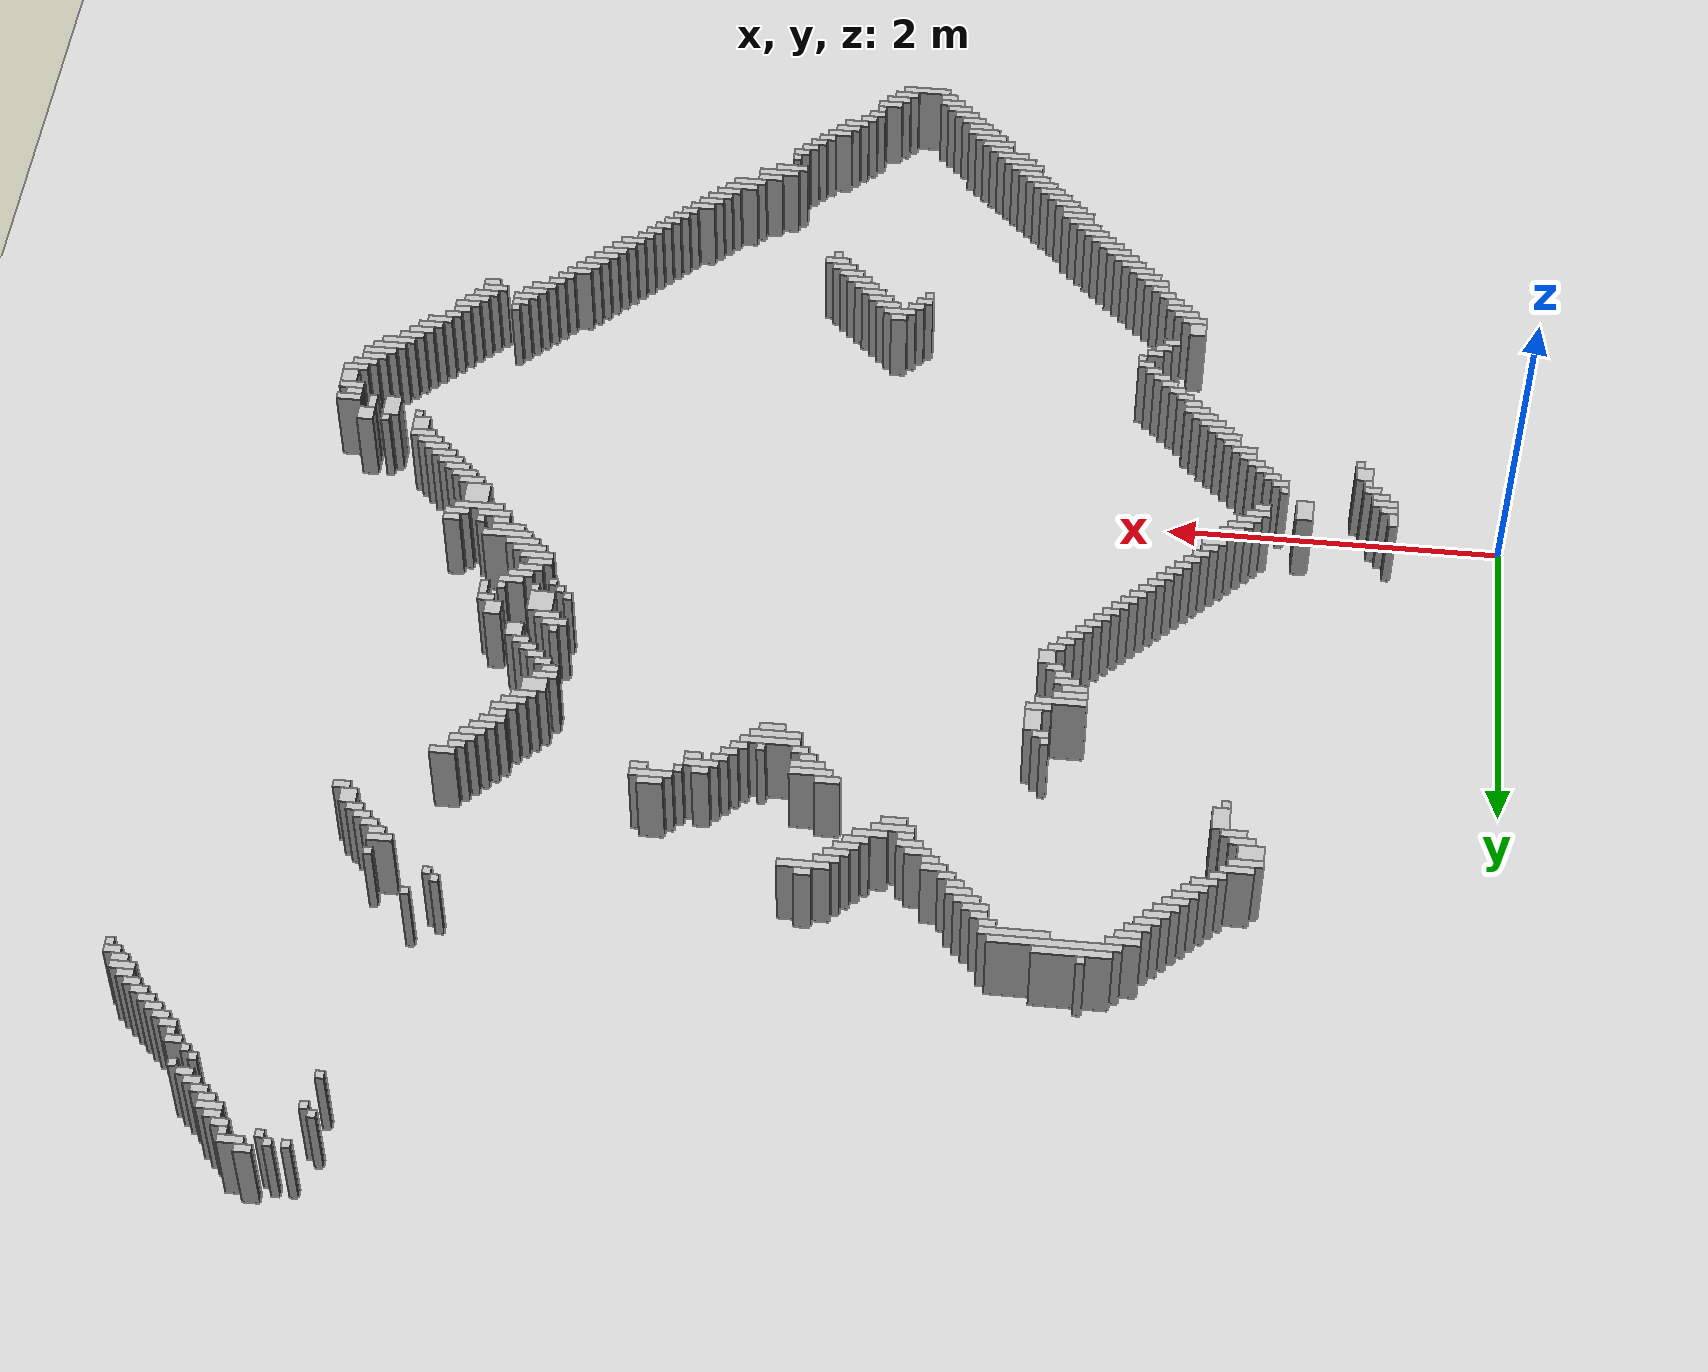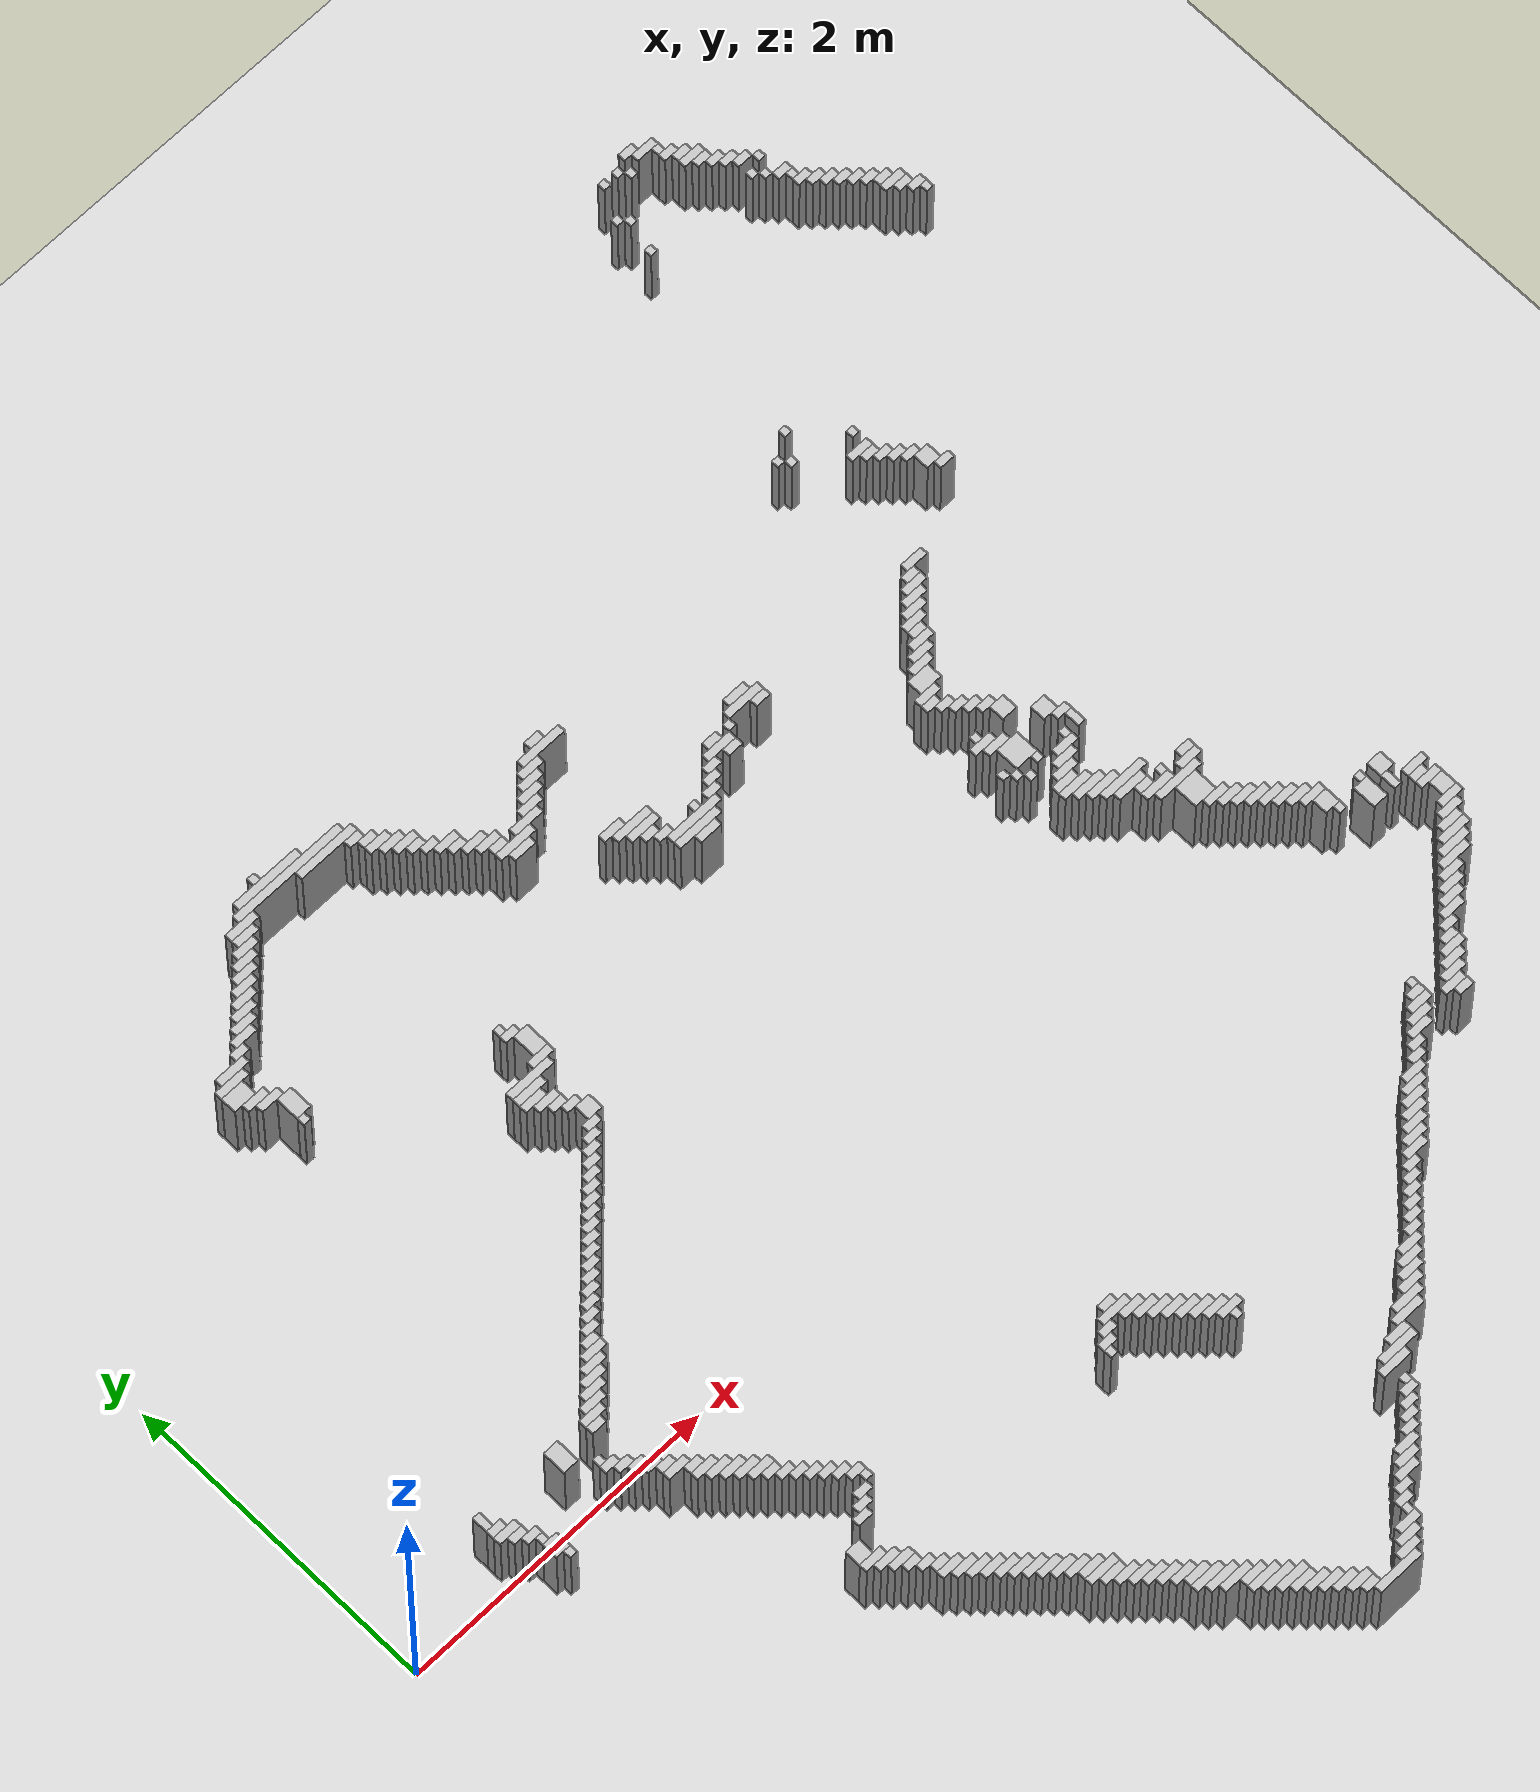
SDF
<?xml version="1.0"?>
<!-- generated by scripts/map_to_world.py from ros2_ws/src/ackermann_bringup/maps/room: 352 wall boxes -->
<sdf version="1.9">
  <world name="room">
    <!-- nothing here falls: the car has no collisions and its dynamics plugin moves it -->
    <gravity>0 0 0</gravity>
    <physics name="1ms" type="ignored">
      <max_step_size>0.001</max_step_size>
      <real_time_factor>1.0</real_time_factor>
    </physics>
    <plugin filename="gz-sim-physics-system" name="gz::sim::systems::Physics"/>
    <plugin filename="gz-sim-user-commands-system" name="gz::sim::systems::UserCommands"/>
    <plugin filename="gz-sim-scene-broadcaster-system" name="gz::sim::systems::SceneBroadcaster"/>
    <plugin filename="gz-sim-sensors-system" name="gz::sim::systems::Sensors">
      <render_engine>ogre2</render_engine>
    </plugin>
    <light type="directional" name="sun">
      <pose>0 0 10 0 0 0</pose>
      <direction>-0.3 0.2 -1</direction>
      <diffuse>0.9 0.9 0.9 1</diffuse>
    </light>
    <model name="ground">
      <static>true</static>
      <link name="link">
        <collision name="c"><geometry><plane><normal>0 0 1</normal><size>30 30</size></plane></geometry></collision>
        <visual name="v"><geometry><plane><normal>0 0 1</normal><size>30 30</size></plane></geometry></visual>
      </link>
    </model>
    <model name="walls">
      <static>true</static>
      <link name="link">
        <collision name="c0"><pose>6.655 5.235 0.25 0 0 0</pose><geometry><box><size>0.100 0.050 0.5</size></box></geometry></collision>
        <visual name="v0"><pose>6.655 5.235 0.25 0 0 0</pose><geometry><box><size>0.100 0.050 0.5</size></box></geometry></visual>
        <collision name="c1"><pose>6.730 5.185 0.25 0 0 0</pose><geometry><box><size>0.150 0.050 0.5</size></box></geometry></collision>
        <visual name="v1"><pose>6.730 5.185 0.25 0 0 0</pose><geometry><box><size>0.150 0.050 0.5</size></box></geometry></visual>
        <collision name="c2"><pose>6.430 5.185 0.25 0 0 0</pose><geometry><box><size>0.050 0.050 0.5</size></box></geometry></collision>
        <visual name="v2"><pose>6.430 5.185 0.25 0 0 0</pose><geometry><box><size>0.050 0.050 0.5</size></box></geometry></visual>
        <collision name="c3"><pose>6.530 5.185 0.25 0 0 0</pose><geometry><box><size>0.050 0.050 0.5</size></box></geometry></collision>
        <visual name="v3"><pose>6.530 5.185 0.25 0 0 0</pose><geometry><box><size>0.050 0.050 0.5</size></box></geometry></visual>
        <collision name="c4"><pose>6.580 5.135 0.25 0 0 0</pose><geometry><box><size>0.050 0.050 0.5</size></box></geometry></collision>
        <visual name="v4"><pose>6.580 5.135 0.25 0 0 0</pose><geometry><box><size>0.050 0.050 0.5</size></box></geometry></visual>
        <collision name="c5"><pose>6.780 5.135 0.25 0 0 0</pose><geometry><box><size>0.050 0.050 0.5</size></box></geometry></collision>
        <visual name="v5"><pose>6.780 5.135 0.25 0 0 0</pose><geometry><box><size>0.050 0.050 0.5</size></box></geometry></visual>
        <collision name="c6"><pose>6.805 5.085 0.25 0 0 0</pose><geometry><box><size>0.100 0.050 0.5</size></box></geometry></collision>
        <visual name="v6"><pose>6.805 5.085 0.25 0 0 0</pose><geometry><box><size>0.100 0.050 0.5</size></box></geometry></visual>
        <collision name="c7"><pose>6.855 5.035 0.25 0 0 0</pose><geometry><box><size>0.100 0.050 0.5</size></box></geometry></collision>
        <visual name="v7"><pose>6.855 5.035 0.25 0 0 0</pose><geometry><box><size>0.100 0.050 0.5</size></box></geometry></visual>
        <collision name="c8"><pose>6.880 4.985 0.25 0 0 0</pose><geometry><box><size>0.150 0.050 0.5</size></box></geometry></collision>
        <visual name="v8"><pose>6.880 4.985 0.25 0 0 0</pose><geometry><box><size>0.150 0.050 0.5</size></box></geometry></visual>
        <collision name="c9"><pose>6.330 4.985 0.25 0 0 0</pose><geometry><box><size>0.050 0.050 0.5</size></box></geometry></collision>
        <visual name="v9"><pose>6.330 4.985 0.25 0 0 0</pose><geometry><box><size>0.050 0.050 0.5</size></box></geometry></visual>
        <collision name="c10"><pose>6.380 4.935 0.25 0 0 0</pose><geometry><box><size>0.050 0.050 0.5</size></box></geometry></collision>
        <visual name="v10"><pose>6.380 4.935 0.25 0 0 0</pose><geometry><box><size>0.050 0.050 0.5</size></box></geometry></visual>
        <collision name="c11"><pose>6.905 4.935 0.25 0 0 0</pose><geometry><box><size>0.100 0.050 0.5</size></box></geometry></collision>
        <visual name="v11"><pose>6.905 4.935 0.25 0 0 0</pose><geometry><box><size>0.100 0.050 0.5</size></box></geometry></visual>
        <collision name="c12"><pose>6.955 4.885 0.25 0 0 0</pose><geometry><box><size>0.100 0.050 0.5</size></box></geometry></collision>
        <visual name="v12"><pose>6.955 4.885 0.25 0 0 0</pose><geometry><box><size>0.100 0.050 0.5</size></box></geometry></visual>
        <collision name="c13"><pose>7.005 4.835 0.25 0 0 0</pose><geometry><box><size>0.100 0.050 0.5</size></box></geometry></collision>
        <visual name="v13"><pose>7.005 4.835 0.25 0 0 0</pose><geometry><box><size>0.100 0.050 0.5</size></box></geometry></visual>
        <collision name="c14"><pose>7.055 4.785 0.25 0 0 0</pose><geometry><box><size>0.100 0.050 0.5</size></box></geometry></collision>
        <visual name="v14"><pose>7.055 4.785 0.25 0 0 0</pose><geometry><box><size>0.100 0.050 0.5</size></box></geometry></visual>
        <collision name="c15"><pose>7.130 4.735 0.25 0 0 0</pose><geometry><box><size>0.050 0.050 0.5</size></box></geometry></collision>
        <visual name="v15"><pose>7.130 4.735 0.25 0 0 0</pose><geometry><box><size>0.050 0.050 0.5</size></box></geometry></visual>
        <collision name="c16"><pose>6.330 4.735 0.25 0 0 0</pose><geometry><box><size>0.050 0.050 0.5</size></box></geometry></collision>
        <visual name="v16"><pose>6.330 4.735 0.25 0 0 0</pose><geometry><box><size>0.050 0.050 0.5</size></box></geometry></visual>
        <collision name="c17"><pose>7.030 4.685 0.25 0 0 0</pose><geometry><box><size>0.050 0.050 0.5</size></box></geometry></collision>
        <visual name="v17"><pose>7.030 4.685 0.25 0 0 0</pose><geometry><box><size>0.050 0.050 0.5</size></box></geometry></visual>
        <collision name="c18"><pose>7.080 4.635 0.25 0 0 0</pose><geometry><box><size>0.050 0.050 0.5</size></box></geometry></collision>
        <visual name="v18"><pose>7.080 4.635 0.25 0 0 0</pose><geometry><box><size>0.050 0.050 0.5</size></box></geometry></visual>
        <collision name="c19"><pose>7.155 4.585 0.25 0 0 0</pose><geometry><box><size>0.100 0.050 0.5</size></box></geometry></collision>
        <visual name="v19"><pose>7.155 4.585 0.25 0 0 0</pose><geometry><box><size>0.100 0.050 0.5</size></box></geometry></visual>
        <collision name="c20"><pose>7.180 4.535 0.25 0 0 0</pose><geometry><box><size>0.050 0.050 0.5</size></box></geometry></collision>
        <visual name="v20"><pose>7.180 4.535 0.25 0 0 0</pose><geometry><box><size>0.050 0.050 0.5</size></box></geometry></visual>
        <collision name="c21"><pose>7.205 4.485 0.25 0 0 0</pose><geometry><box><size>0.100 0.050 0.5</size></box></geometry></collision>
        <visual name="v21"><pose>7.205 4.485 0.25 0 0 0</pose><geometry><box><size>0.100 0.050 0.5</size></box></geometry></visual>
        <collision name="c22"><pose>7.255 4.435 0.25 0 0 0</pose><geometry><box><size>0.100 0.050 0.5</size></box></geometry></collision>
        <visual name="v22"><pose>7.255 4.435 0.25 0 0 0</pose><geometry><box><size>0.100 0.050 0.5</size></box></geometry></visual>
        <collision name="c23"><pose>7.305 4.385 0.25 0 0 0</pose><geometry><box><size>0.100 0.050 0.5</size></box></geometry></collision>
        <visual name="v23"><pose>7.305 4.385 0.25 0 0 0</pose><geometry><box><size>0.100 0.050 0.5</size></box></geometry></visual>
        <collision name="c24"><pose>7.355 4.335 0.25 0 0 0</pose><geometry><box><size>0.100 0.050 0.5</size></box></geometry></collision>
        <visual name="v24"><pose>7.355 4.335 0.25 0 0 0</pose><geometry><box><size>0.100 0.050 0.5</size></box></geometry></visual>
        <collision name="c25"><pose>7.405 4.285 0.25 0 0 0</pose><geometry><box><size>0.100 0.050 0.5</size></box></geometry></collision>
        <visual name="v25"><pose>7.405 4.285 0.25 0 0 0</pose><geometry><box><size>0.100 0.050 0.5</size></box></geometry></visual>
        <collision name="c26"><pose>7.455 4.235 0.25 0 0 0</pose><geometry><box><size>0.100 0.050 0.5</size></box></geometry></collision>
        <visual name="v26"><pose>7.455 4.235 0.25 0 0 0</pose><geometry><box><size>0.100 0.050 0.5</size></box></geometry></visual>
        <collision name="c27"><pose>7.505 4.185 0.25 0 0 0</pose><geometry><box><size>0.100 0.050 0.5</size></box></geometry></collision>
        <visual name="v27"><pose>7.505 4.185 0.25 0 0 0</pose><geometry><box><size>0.100 0.050 0.5</size></box></geometry></visual>
        <collision name="c28"><pose>7.530 4.135 0.25 0 0 0</pose><geometry><box><size>0.150 0.050 0.5</size></box></geometry></collision>
        <visual name="v28"><pose>7.530 4.135 0.25 0 0 0</pose><geometry><box><size>0.150 0.050 0.5</size></box></geometry></visual>
        <collision name="c29"><pose>7.555 4.085 0.25 0 0 0</pose><geometry><box><size>0.100 0.050 0.5</size></box></geometry></collision>
        <visual name="v29"><pose>7.555 4.085 0.25 0 0 0</pose><geometry><box><size>0.100 0.050 0.5</size></box></geometry></visual>
        <collision name="c30"><pose>7.605 4.035 0.25 0 0 0</pose><geometry><box><size>0.100 0.050 0.5</size></box></geometry></collision>
        <visual name="v30"><pose>7.605 4.035 0.25 0 0 0</pose><geometry><box><size>0.100 0.050 0.5</size></box></geometry></visual>
        <collision name="c31"><pose>7.630 3.985 0.25 0 0 0</pose><geometry><box><size>0.050 0.050 0.5</size></box></geometry></collision>
        <visual name="v31"><pose>7.630 3.985 0.25 0 0 0</pose><geometry><box><size>0.050 0.050 0.5</size></box></geometry></visual>
        <collision name="c32"><pose>2.330 3.585 0.25 0 0 0</pose><geometry><box><size>0.050 0.050 0.5</size></box></geometry></collision>
        <visual name="v32"><pose>2.330 3.585 0.25 0 0 0</pose><geometry><box><size>0.050 0.050 0.5</size></box></geometry></visual>
        <collision name="c33"><pose>2.380 3.535 0.25 0 0 0</pose><geometry><box><size>0.450 0.050 0.5</size></box></geometry></collision>
        <visual name="v33"><pose>2.380 3.535 0.25 0 0 0</pose><geometry><box><size>0.450 0.050 0.5</size></box></geometry></visual>
        <collision name="c34"><pose>2.480 3.485 0.25 0 0 0</pose><geometry><box><size>0.750 0.050 0.5</size></box></geometry></collision>
        <visual name="v34"><pose>2.480 3.485 0.25 0 0 0</pose><geometry><box><size>0.750 0.050 0.5</size></box></geometry></visual>
        <collision name="c35"><pose>6.080 3.485 0.25 0 0 0</pose><geometry><box><size>0.050 0.050 0.5</size></box></geometry></collision>
        <visual name="v35"><pose>6.080 3.485 0.25 0 0 0</pose><geometry><box><size>0.050 0.050 0.5</size></box></geometry></visual>
        <collision name="c36"><pose>2.105 3.435 0.25 0 0 0</pose><geometry><box><size>0.200 0.050 0.5</size></box></geometry></collision>
        <visual name="v36"><pose>2.105 3.435 0.25 0 0 0</pose><geometry><box><size>0.200 0.050 0.5</size></box></geometry></visual>
        <collision name="c37"><pose>2.705 3.435 0.25 0 0 0</pose><geometry><box><size>0.400 0.050 0.5</size></box></geometry></collision>
        <visual name="v37"><pose>2.705 3.435 0.25 0 0 0</pose><geometry><box><size>0.400 0.050 0.5</size></box></geometry></visual>
        <collision name="c38"><pose>5.930 3.385 0.25 0 0 0</pose><geometry><box><size>0.050 0.050 0.5</size></box></geometry></collision>
        <visual name="v38"><pose>5.930 3.385 0.25 0 0 0</pose><geometry><box><size>0.050 0.050 0.5</size></box></geometry></visual>
        <collision name="c39"><pose>2.855 3.385 0.25 0 0 0</pose><geometry><box><size>0.100 0.050 0.5</size></box></geometry></collision>
        <visual name="v39"><pose>2.855 3.385 0.25 0 0 0</pose><geometry><box><size>0.100 0.050 0.5</size></box></geometry></visual>
        <collision name="c40"><pose>2.080 3.385 0.25 0 0 0</pose><geometry><box><size>0.150 0.050 0.5</size></box></geometry></collision>
        <visual name="v40"><pose>2.080 3.385 0.25 0 0 0</pose><geometry><box><size>0.150 0.050 0.5</size></box></geometry></visual>
        <collision name="c41"><pose>2.905 3.335 0.25 0 0 0</pose><geometry><box><size>0.100 0.050 0.5</size></box></geometry></collision>
        <visual name="v41"><pose>2.905 3.335 0.25 0 0 0</pose><geometry><box><size>0.100 0.050 0.5</size></box></geometry></visual>
        <collision name="c42"><pose>2.030 3.335 0.25 0 0 0</pose><geometry><box><size>0.150 0.050 0.5</size></box></geometry></collision>
        <visual name="v42"><pose>2.030 3.335 0.25 0 0 0</pose><geometry><box><size>0.150 0.050 0.5</size></box></geometry></visual>
        <collision name="c43"><pose>5.980 3.335 0.25 0 0 0</pose><geometry><box><size>0.050 0.050 0.5</size></box></geometry></collision>
        <visual name="v43"><pose>5.980 3.335 0.25 0 0 0</pose><geometry><box><size>0.050 0.050 0.5</size></box></geometry></visual>
        <collision name="c44"><pose>2.930 3.285 0.25 0 0 0</pose><geometry><box><size>0.150 0.050 0.5</size></box></geometry></collision>
        <visual name="v44"><pose>2.930 3.285 0.25 0 0 0</pose><geometry><box><size>0.150 0.050 0.5</size></box></geometry></visual>
        <collision name="c45"><pose>1.980 3.285 0.25 0 0 0</pose><geometry><box><size>0.150 0.050 0.5</size></box></geometry></collision>
        <visual name="v45"><pose>1.980 3.285 0.25 0 0 0</pose><geometry><box><size>0.150 0.050 0.5</size></box></geometry></visual>
        <collision name="c46"><pose>1.930 3.235 0.25 0 0 0</pose><geometry><box><size>0.150 0.050 0.5</size></box></geometry></collision>
        <visual name="v46"><pose>1.930 3.235 0.25 0 0 0</pose><geometry><box><size>0.150 0.050 0.5</size></box></geometry></visual>
        <collision name="c47"><pose>6.330 3.235 0.25 0 0 0</pose><geometry><box><size>0.050 0.050 0.5</size></box></geometry></collision>
        <visual name="v47"><pose>6.330 3.235 0.25 0 0 0</pose><geometry><box><size>0.050 0.050 0.5</size></box></geometry></visual>
        <collision name="c48"><pose>2.980 3.235 0.25 0 0 0</pose><geometry><box><size>0.150 0.050 0.5</size></box></geometry></collision>
        <visual name="v48"><pose>2.980 3.235 0.25 0 0 0</pose><geometry><box><size>0.150 0.050 0.5</size></box></geometry></visual>
        <collision name="c49"><pose>3.030 3.185 0.25 0 0 0</pose><geometry><box><size>0.150 0.050 0.5</size></box></geometry></collision>
        <visual name="v49"><pose>3.030 3.185 0.25 0 0 0</pose><geometry><box><size>0.150 0.050 0.5</size></box></geometry></visual>
        <collision name="c50"><pose>1.880 3.185 0.25 0 0 0</pose><geometry><box><size>0.150 0.050 0.5</size></box></geometry></collision>
        <visual name="v50"><pose>1.880 3.185 0.25 0 0 0</pose><geometry><box><size>0.150 0.050 0.5</size></box></geometry></visual>
        <collision name="c51"><pose>1.830 3.135 0.25 0 0 0</pose><geometry><box><size>0.150 0.050 0.5</size></box></geometry></collision>
        <visual name="v51"><pose>1.830 3.135 0.25 0 0 0</pose><geometry><box><size>0.150 0.050 0.5</size></box></geometry></visual>
        <collision name="c52"><pose>3.055 3.135 0.25 0 0 0</pose><geometry><box><size>0.100 0.050 0.5</size></box></geometry></collision>
        <visual name="v52"><pose>3.055 3.135 0.25 0 0 0</pose><geometry><box><size>0.100 0.050 0.5</size></box></geometry></visual>
        <collision name="c53"><pose>6.280 3.135 0.25 0 0 0</pose><geometry><box><size>0.150 0.050 0.5</size></box></geometry></collision>
        <visual name="v53"><pose>6.280 3.135 0.25 0 0 0</pose><geometry><box><size>0.150 0.050 0.5</size></box></geometry></visual>
        <collision name="c54"><pose>3.905 3.135 0.25 0 0 0</pose><geometry><box><size>0.100 0.050 0.5</size></box></geometry></collision>
        <visual name="v54"><pose>3.905 3.135 0.25 0 0 0</pose><geometry><box><size>0.100 0.050 0.5</size></box></geometry></visual>
        <collision name="c55"><pose>3.105 3.085 0.25 0 0 0</pose><geometry><box><size>0.100 0.050 0.5</size></box></geometry></collision>
        <visual name="v55"><pose>3.105 3.085 0.25 0 0 0</pose><geometry><box><size>0.100 0.050 0.5</size></box></geometry></visual>
        <collision name="c56"><pose>3.905 3.085 0.25 0 0 0</pose><geometry><box><size>0.300 0.050 0.5</size></box></geometry></collision>
        <visual name="v56"><pose>3.905 3.085 0.25 0 0 0</pose><geometry><box><size>0.300 0.050 0.5</size></box></geometry></visual>
        <collision name="c57"><pose>6.305 3.085 0.25 0 0 0</pose><geometry><box><size>0.100 0.050 0.5</size></box></geometry></collision>
        <visual name="v57"><pose>6.305 3.085 0.25 0 0 0</pose><geometry><box><size>0.100 0.050 0.5</size></box></geometry></visual>
        <collision name="c58"><pose>1.780 3.085 0.25 0 0 0</pose><geometry><box><size>0.150 0.050 0.5</size></box></geometry></collision>
        <visual name="v58"><pose>1.780 3.085 0.25 0 0 0</pose><geometry><box><size>0.150 0.050 0.5</size></box></geometry></visual>
        <collision name="c59"><pose>1.730 3.035 0.25 0 0 0</pose><geometry><box><size>0.150 0.050 0.5</size></box></geometry></collision>
        <visual name="v59"><pose>1.730 3.035 0.25 0 0 0</pose><geometry><box><size>0.150 0.050 0.5</size></box></geometry></visual>
        <collision name="c60"><pose>3.780 3.035 0.25 0 0 0</pose><geometry><box><size>0.150 0.050 0.5</size></box></geometry></collision>
        <visual name="v60"><pose>3.780 3.035 0.25 0 0 0</pose><geometry><box><size>0.150 0.050 0.5</size></box></geometry></visual>
        <collision name="c61"><pose>6.355 3.035 0.25 0 0 0</pose><geometry><box><size>0.100 0.050 0.5</size></box></geometry></collision>
        <visual name="v61"><pose>6.355 3.035 0.25 0 0 0</pose><geometry><box><size>0.100 0.050 0.5</size></box></geometry></visual>
        <collision name="c62"><pose>3.180 3.035 0.25 0 0 0</pose><geometry><box><size>0.150 0.050 0.5</size></box></geometry></collision>
        <visual name="v62"><pose>3.180 3.035 0.25 0 0 0</pose><geometry><box><size>0.150 0.050 0.5</size></box></geometry></visual>
        <collision name="c63"><pose>6.405 2.985 0.25 0 0 0</pose><geometry><box><size>0.100 0.050 0.5</size></box></geometry></collision>
        <visual name="v63"><pose>6.405 2.985 0.25 0 0 0</pose><geometry><box><size>0.100 0.050 0.5</size></box></geometry></visual>
        <collision name="c64"><pose>3.205 2.985 0.25 0 0 0</pose><geometry><box><size>0.100 0.050 0.5</size></box></geometry></collision>
        <visual name="v64"><pose>3.205 2.985 0.25 0 0 0</pose><geometry><box><size>0.100 0.050 0.5</size></box></geometry></visual>
        <collision name="c65"><pose>1.680 2.985 0.25 0 0 0</pose><geometry><box><size>0.150 0.050 0.5</size></box></geometry></collision>
        <visual name="v65"><pose>1.680 2.985 0.25 0 0 0</pose><geometry><box><size>0.150 0.050 0.5</size></box></geometry></visual>
        <collision name="c66"><pose>3.730 2.985 0.25 0 0 0</pose><geometry><box><size>0.150 0.050 0.5</size></box></geometry></collision>
        <visual name="v66"><pose>3.730 2.985 0.25 0 0 0</pose><geometry><box><size>0.150 0.050 0.5</size></box></geometry></visual>
        <collision name="c67"><pose>3.680 2.935 0.25 0 0 0</pose><geometry><box><size>0.150 0.050 0.5</size></box></geometry></collision>
        <visual name="v67"><pose>3.680 2.935 0.25 0 0 0</pose><geometry><box><size>0.150 0.050 0.5</size></box></geometry></visual>
        <collision name="c68"><pose>6.455 2.935 0.25 0 0 0</pose><geometry><box><size>0.100 0.050 0.5</size></box></geometry></collision>
        <visual name="v68"><pose>6.455 2.935 0.25 0 0 0</pose><geometry><box><size>0.100 0.050 0.5</size></box></geometry></visual>
        <collision name="c69"><pose>1.605 2.935 0.25 0 0 0</pose><geometry><box><size>0.100 0.050 0.5</size></box></geometry></collision>
        <visual name="v69"><pose>1.605 2.935 0.25 0 0 0</pose><geometry><box><size>0.100 0.050 0.5</size></box></geometry></visual>
        <collision name="c70"><pose>3.280 2.935 0.25 0 0 0</pose><geometry><box><size>0.150 0.050 0.5</size></box></geometry></collision>
        <visual name="v70"><pose>3.280 2.935 0.25 0 0 0</pose><geometry><box><size>0.150 0.050 0.5</size></box></geometry></visual>
        <collision name="c71"><pose>3.330 2.885 0.25 0 0 0</pose><geometry><box><size>0.150 0.050 0.5</size></box></geometry></collision>
        <visual name="v71"><pose>3.330 2.885 0.25 0 0 0</pose><geometry><box><size>0.150 0.050 0.5</size></box></geometry></visual>
        <collision name="c72"><pose>1.505 2.885 0.25 0 0 0</pose><geometry><box><size>0.200 0.050 0.5</size></box></geometry></collision>
        <visual name="v72"><pose>1.505 2.885 0.25 0 0 0</pose><geometry><box><size>0.200 0.050 0.5</size></box></geometry></visual>
        <collision name="c73"><pose>3.630 2.885 0.25 0 0 0</pose><geometry><box><size>0.150 0.050 0.5</size></box></geometry></collision>
        <visual name="v73"><pose>3.630 2.885 0.25 0 0 0</pose><geometry><box><size>0.150 0.050 0.5</size></box></geometry></visual>
        <collision name="c74"><pose>6.505 2.860 0.25 0 0 0</pose><geometry><box><size>0.100 0.100 0.5</size></box></geometry></collision>
        <visual name="v74"><pose>6.505 2.860 0.25 0 0 0</pose><geometry><box><size>0.100 0.100 0.5</size></box></geometry></visual>
        <collision name="c75"><pose>3.555 2.835 0.25 0 0 0</pose><geometry><box><size>0.200 0.050 0.5</size></box></geometry></collision>
        <visual name="v75"><pose>3.555 2.835 0.25 0 0 0</pose><geometry><box><size>0.200 0.050 0.5</size></box></geometry></visual>
        <collision name="c76"><pose>3.355 2.835 0.25 0 0 0</pose><geometry><box><size>0.100 0.050 0.5</size></box></geometry></collision>
        <visual name="v76"><pose>3.355 2.835 0.25 0 0 0</pose><geometry><box><size>0.100 0.050 0.5</size></box></geometry></visual>
        <collision name="c77"><pose>1.455 2.835 0.25 0 0 0</pose><geometry><box><size>0.200 0.050 0.5</size></box></geometry></collision>
        <visual name="v77"><pose>1.455 2.835 0.25 0 0 0</pose><geometry><box><size>0.200 0.050 0.5</size></box></geometry></visual>
        <collision name="c78"><pose>3.430 2.785 0.25 0 0 0</pose><geometry><box><size>0.250 0.050 0.5</size></box></geometry></collision>
        <visual name="v78"><pose>3.430 2.785 0.25 0 0 0</pose><geometry><box><size>0.250 0.050 0.5</size></box></geometry></visual>
        <collision name="c79"><pose>6.555 2.785 0.25 0 0 0</pose><geometry><box><size>0.100 0.050 0.5</size></box></geometry></collision>
        <visual name="v79"><pose>6.555 2.785 0.25 0 0 0</pose><geometry><box><size>0.100 0.050 0.5</size></box></geometry></visual>
        <collision name="c80"><pose>1.430 2.760 0.25 0 0 0</pose><geometry><box><size>0.150 0.100 0.5</size></box></geometry></collision>
        <visual name="v80"><pose>1.430 2.760 0.25 0 0 0</pose><geometry><box><size>0.150 0.100 0.5</size></box></geometry></visual>
        <collision name="c81"><pose>3.430 2.735 0.25 0 0 0</pose><geometry><box><size>0.150 0.050 0.5</size></box></geometry></collision>
        <visual name="v81"><pose>3.430 2.735 0.25 0 0 0</pose><geometry><box><size>0.150 0.050 0.5</size></box></geometry></visual>
        <collision name="c82"><pose>1.480 2.685 0.25 0 0 0</pose><geometry><box><size>0.150 0.050 0.5</size></box></geometry></collision>
        <visual name="v82"><pose>1.480 2.685 0.25 0 0 0</pose><geometry><box><size>0.150 0.050 0.5</size></box></geometry></visual>
        <collision name="c83"><pose>1.530 2.635 0.25 0 0 0</pose><geometry><box><size>0.150 0.050 0.5</size></box></geometry></collision>
        <visual name="v83"><pose>1.530 2.635 0.25 0 0 0</pose><geometry><box><size>0.150 0.050 0.5</size></box></geometry></visual>
        <collision name="c84"><pose>4.830 2.585 0.25 0 0 0</pose><geometry><box><size>0.150 0.050 0.5</size></box></geometry></collision>
        <visual name="v84"><pose>4.830 2.585 0.25 0 0 0</pose><geometry><box><size>0.150 0.050 0.5</size></box></geometry></visual>
        <collision name="c85"><pose>4.830 2.535 0.25 0 0 0</pose><geometry><box><size>0.250 0.050 0.5</size></box></geometry></collision>
        <visual name="v85"><pose>4.830 2.535 0.25 0 0 0</pose><geometry><box><size>0.250 0.050 0.5</size></box></geometry></visual>
        <collision name="c86"><pose>1.605 2.535 0.25 0 0 0</pose><geometry><box><size>0.100 0.150 0.5</size></box></geometry></collision>
        <visual name="v86"><pose>1.605 2.535 0.25 0 0 0</pose><geometry><box><size>0.100 0.150 0.5</size></box></geometry></visual>
        <collision name="c87"><pose>4.555 2.485 0.25 0 0 0</pose><geometry><box><size>0.100 0.050 0.5</size></box></geometry></collision>
        <visual name="v87"><pose>4.555 2.485 0.25 0 0 0</pose><geometry><box><size>0.100 0.050 0.5</size></box></geometry></visual>
        <collision name="c88"><pose>3.830 2.485 0.25 0 0 0</pose><geometry><box><size>0.150 0.050 0.5</size></box></geometry></collision>
        <visual name="v88"><pose>3.830 2.485 0.25 0 0 0</pose><geometry><box><size>0.150 0.050 0.5</size></box></geometry></visual>
        <collision name="c89"><pose>4.680 2.485 0.25 0 0 0</pose><geometry><box><size>0.050 0.050 0.5</size></box></geometry></collision>
        <visual name="v89"><pose>4.680 2.485 0.25 0 0 0</pose><geometry><box><size>0.050 0.050 0.5</size></box></geometry></visual>
        <collision name="c90"><pose>6.030 2.485 0.25 0 0 0</pose><geometry><box><size>0.150 0.050 0.5</size></box></geometry></collision>
        <visual name="v90"><pose>6.030 2.485 0.25 0 0 0</pose><geometry><box><size>0.150 0.050 0.5</size></box></geometry></visual>
        <collision name="c91"><pose>4.905 2.485 0.25 0 0 0</pose><geometry><box><size>0.100 0.050 0.5</size></box></geometry></collision>
        <visual name="v91"><pose>4.905 2.485 0.25 0 0 0</pose><geometry><box><size>0.100 0.050 0.5</size></box></geometry></visual>
        <collision name="c92"><pose>3.930 2.435 0.25 0 0 0</pose><geometry><box><size>0.250 0.050 0.5</size></box></geometry></collision>
        <visual name="v92"><pose>3.930 2.435 0.25 0 0 0</pose><geometry><box><size>0.250 0.050 0.5</size></box></geometry></visual>
        <collision name="c93"><pose>5.955 2.435 0.25 0 0 0</pose><geometry><box><size>0.100 0.050 0.5</size></box></geometry></collision>
        <visual name="v93"><pose>5.955 2.435 0.25 0 0 0</pose><geometry><box><size>0.100 0.050 0.5</size></box></geometry></visual>
        <collision name="c94"><pose>1.580 2.435 0.25 0 0 0</pose><geometry><box><size>0.050 0.050 0.5</size></box></geometry></collision>
        <visual name="v94"><pose>1.580 2.435 0.25 0 0 0</pose><geometry><box><size>0.050 0.050 0.5</size></box></geometry></visual>
        <collision name="c95"><pose>4.555 2.435 0.25 0 0 0</pose><geometry><box><size>0.200 0.050 0.5</size></box></geometry></collision>
        <visual name="v95"><pose>4.555 2.435 0.25 0 0 0</pose><geometry><box><size>0.200 0.050 0.5</size></box></geometry></visual>
        <collision name="c96"><pose>4.455 2.385 0.25 0 0 0</pose><geometry><box><size>0.100 0.050 0.5</size></box></geometry></collision>
        <visual name="v96"><pose>4.455 2.385 0.25 0 0 0</pose><geometry><box><size>0.100 0.050 0.5</size></box></geometry></visual>
        <collision name="c97"><pose>3.955 2.385 0.25 0 0 0</pose><geometry><box><size>0.200 0.050 0.5</size></box></geometry></collision>
        <visual name="v97"><pose>3.955 2.385 0.25 0 0 0</pose><geometry><box><size>0.200 0.050 0.5</size></box></geometry></visual>
        <collision name="c98"><pose>5.930 2.385 0.25 0 0 0</pose><geometry><box><size>0.150 0.050 0.5</size></box></geometry></collision>
        <visual name="v98"><pose>5.930 2.385 0.25 0 0 0</pose><geometry><box><size>0.150 0.050 0.5</size></box></geometry></visual>
        <collision name="c99"><pose>4.605 2.385 0.25 0 0 0</pose><geometry><box><size>0.100 0.050 0.5</size></box></geometry></collision>
        <visual name="v99"><pose>4.605 2.385 0.25 0 0 0</pose><geometry><box><size>0.100 0.050 0.5</size></box></geometry></visual>
        <collision name="c100"><pose>5.880 2.335 0.25 0 0 0</pose><geometry><box><size>0.150 0.050 0.5</size></box></geometry></collision>
        <visual name="v100"><pose>5.880 2.335 0.25 0 0 0</pose><geometry><box><size>0.150 0.050 0.5</size></box></geometry></visual>
        <collision name="c101"><pose>4.405 2.335 0.25 0 0 0</pose><geometry><box><size>0.100 0.050 0.5</size></box></geometry></collision>
        <visual name="v101"><pose>4.405 2.335 0.25 0 0 0</pose><geometry><box><size>0.100 0.050 0.5</size></box></geometry></visual>
        <collision name="c102"><pose>3.955 2.335 0.25 0 0 0</pose><geometry><box><size>0.100 0.050 0.5</size></box></geometry></collision>
        <visual name="v102"><pose>3.955 2.335 0.25 0 0 0</pose><geometry><box><size>0.100 0.050 0.5</size></box></geometry></visual>
        <collision name="c103"><pose>4.005 2.285 0.25 0 0 0</pose><geometry><box><size>0.100 0.050 0.5</size></box></geometry></collision>
        <visual name="v103"><pose>4.005 2.285 0.25 0 0 0</pose><geometry><box><size>0.100 0.050 0.5</size></box></geometry></visual>
        <collision name="c104"><pose>5.830 2.285 0.25 0 0 0</pose><geometry><box><size>0.150 0.050 0.5</size></box></geometry></collision>
        <visual name="v104"><pose>5.830 2.285 0.25 0 0 0</pose><geometry><box><size>0.150 0.050 0.5</size></box></geometry></visual>
        <collision name="c105"><pose>4.230 2.285 0.25 0 0 0</pose><geometry><box><size>0.050 0.050 0.5</size></box></geometry></collision>
        <visual name="v105"><pose>4.230 2.285 0.25 0 0 0</pose><geometry><box><size>0.050 0.050 0.5</size></box></geometry></visual>
        <collision name="c106"><pose>4.355 2.285 0.25 0 0 0</pose><geometry><box><size>0.100 0.050 0.5</size></box></geometry></collision>
        <visual name="v106"><pose>4.355 2.285 0.25 0 0 0</pose><geometry><box><size>0.100 0.050 0.5</size></box></geometry></visual>
        <collision name="c107"><pose>5.780 2.235 0.25 0 0 0</pose><geometry><box><size>0.150 0.050 0.5</size></box></geometry></collision>
        <visual name="v107"><pose>5.780 2.235 0.25 0 0 0</pose><geometry><box><size>0.150 0.050 0.5</size></box></geometry></visual>
        <collision name="c108"><pose>4.180 2.235 0.25 0 0 0</pose><geometry><box><size>0.350 0.050 0.5</size></box></geometry></collision>
        <visual name="v108"><pose>4.180 2.235 0.25 0 0 0</pose><geometry><box><size>0.350 0.050 0.5</size></box></geometry></visual>
        <collision name="c109"><pose>5.755 2.185 0.25 0 0 0</pose><geometry><box><size>0.100 0.050 0.5</size></box></geometry></collision>
        <visual name="v109"><pose>5.755 2.185 0.25 0 0 0</pose><geometry><box><size>0.100 0.050 0.5</size></box></geometry></visual>
        <collision name="c110"><pose>4.155 2.185 0.25 0 0 0</pose><geometry><box><size>0.300 0.050 0.5</size></box></geometry></collision>
        <visual name="v110"><pose>4.155 2.185 0.25 0 0 0</pose><geometry><box><size>0.300 0.050 0.5</size></box></geometry></visual>
        <collision name="c111"><pose>5.730 2.135 0.25 0 0 0</pose><geometry><box><size>0.150 0.050 0.5</size></box></geometry></collision>
        <visual name="v111"><pose>5.730 2.135 0.25 0 0 0</pose><geometry><box><size>0.150 0.050 0.5</size></box></geometry></visual>
        <collision name="c112"><pose>4.180 2.135 0.25 0 0 0</pose><geometry><box><size>0.150 0.050 0.5</size></box></geometry></collision>
        <visual name="v112"><pose>4.180 2.135 0.25 0 0 0</pose><geometry><box><size>0.150 0.050 0.5</size></box></geometry></visual>
        <collision name="c113"><pose>2.630 2.085 0.25 0 0 0</pose><geometry><box><size>0.050 0.050 0.5</size></box></geometry></collision>
        <visual name="v113"><pose>2.630 2.085 0.25 0 0 0</pose><geometry><box><size>0.050 0.050 0.5</size></box></geometry></visual>
        <collision name="c114"><pose>5.680 2.085 0.25 0 0 0</pose><geometry><box><size>0.150 0.050 0.5</size></box></geometry></collision>
        <visual name="v114"><pose>5.680 2.085 0.25 0 0 0</pose><geometry><box><size>0.150 0.050 0.5</size></box></geometry></visual>
        <collision name="c115"><pose>2.655 2.035 0.25 0 0 0</pose><geometry><box><size>0.100 0.050 0.5</size></box></geometry></collision>
        <visual name="v115"><pose>2.655 2.035 0.25 0 0 0</pose><geometry><box><size>0.100 0.050 0.5</size></box></geometry></visual>
        <collision name="c116"><pose>5.630 2.035 0.25 0 0 0</pose><geometry><box><size>0.150 0.050 0.5</size></box></geometry></collision>
        <visual name="v116"><pose>5.630 2.035 0.25 0 0 0</pose><geometry><box><size>0.150 0.050 0.5</size></box></geometry></visual>
        <collision name="c117"><pose>5.580 1.960 0.25 0 0 0</pose><geometry><box><size>0.150 0.100 0.5</size></box></geometry></collision>
        <visual name="v117"><pose>5.580 1.960 0.25 0 0 0</pose><geometry><box><size>0.150 0.100 0.5</size></box></geometry></visual>
        <collision name="c118"><pose>2.705 1.935 0.25 0 0 0</pose><geometry><box><size>0.100 0.150 0.5</size></box></geometry></collision>
        <visual name="v118"><pose>2.705 1.935 0.25 0 0 0</pose><geometry><box><size>0.100 0.150 0.5</size></box></geometry></visual>
        <collision name="c119"><pose>5.530 1.885 0.25 0 0 0</pose><geometry><box><size>0.150 0.050 0.5</size></box></geometry></collision>
        <visual name="v119"><pose>5.530 1.885 0.25 0 0 0</pose><geometry><box><size>0.150 0.050 0.5</size></box></geometry></visual>
        <collision name="c120"><pose>5.505 1.835 0.25 0 0 0</pose><geometry><box><size>0.100 0.050 0.5</size></box></geometry></collision>
        <visual name="v120"><pose>5.505 1.835 0.25 0 0 0</pose><geometry><box><size>0.100 0.050 0.5</size></box></geometry></visual>
        <collision name="c121"><pose>2.680 1.835 0.25 0 0 0</pose><geometry><box><size>0.150 0.050 0.5</size></box></geometry></collision>
        <visual name="v121"><pose>2.680 1.835 0.25 0 0 0</pose><geometry><box><size>0.150 0.050 0.5</size></box></geometry></visual>
        <collision name="c122"><pose>2.555 1.785 0.25 0 0 0</pose><geometry><box><size>0.300 0.050 0.5</size></box></geometry></collision>
        <visual name="v122"><pose>2.555 1.785 0.25 0 0 0</pose><geometry><box><size>0.300 0.050 0.5</size></box></geometry></visual>
        <collision name="c123"><pose>5.555 1.785 0.25 0 0 0</pose><geometry><box><size>0.100 0.050 0.5</size></box></geometry></collision>
        <visual name="v123"><pose>5.555 1.785 0.25 0 0 0</pose><geometry><box><size>0.100 0.050 0.5</size></box></geometry></visual>
        <collision name="c124"><pose>2.505 1.735 0.25 0 0 0</pose><geometry><box><size>0.200 0.050 0.5</size></box></geometry></collision>
        <visual name="v124"><pose>2.505 1.735 0.25 0 0 0</pose><geometry><box><size>0.200 0.050 0.5</size></box></geometry></visual>
        <collision name="c125"><pose>5.605 1.735 0.25 0 0 0</pose><geometry><box><size>0.100 0.050 0.5</size></box></geometry></collision>
        <visual name="v125"><pose>5.605 1.735 0.25 0 0 0</pose><geometry><box><size>0.100 0.050 0.5</size></box></geometry></visual>
        <collision name="c126"><pose>5.655 1.685 0.25 0 0 0</pose><geometry><box><size>0.100 0.050 0.5</size></box></geometry></collision>
        <visual name="v126"><pose>5.655 1.685 0.25 0 0 0</pose><geometry><box><size>0.100 0.050 0.5</size></box></geometry></visual>
        <collision name="c127"><pose>2.480 1.685 0.25 0 0 0</pose><geometry><box><size>0.150 0.050 0.5</size></box></geometry></collision>
        <visual name="v127"><pose>2.480 1.685 0.25 0 0 0</pose><geometry><box><size>0.150 0.050 0.5</size></box></geometry></visual>
        <collision name="c128"><pose>5.705 1.635 0.25 0 0 0</pose><geometry><box><size>0.100 0.050 0.5</size></box></geometry></collision>
        <visual name="v128"><pose>5.705 1.635 0.25 0 0 0</pose><geometry><box><size>0.100 0.050 0.5</size></box></geometry></visual>
        <collision name="c129"><pose>2.530 1.635 0.25 0 0 0</pose><geometry><box><size>0.150 0.050 0.5</size></box></geometry></collision>
        <visual name="v129"><pose>2.530 1.635 0.25 0 0 0</pose><geometry><box><size>0.150 0.050 0.5</size></box></geometry></visual>
        <collision name="c130"><pose>2.555 1.585 0.25 0 0 0</pose><geometry><box><size>0.100 0.050 0.5</size></box></geometry></collision>
        <visual name="v130"><pose>2.555 1.585 0.25 0 0 0</pose><geometry><box><size>0.100 0.050 0.5</size></box></geometry></visual>
        <collision name="c131"><pose>5.755 1.560 0.25 0 0 0</pose><geometry><box><size>0.100 0.100 0.5</size></box></geometry></collision>
        <visual name="v131"><pose>5.755 1.560 0.25 0 0 0</pose><geometry><box><size>0.100 0.100 0.5</size></box></geometry></visual>
        <collision name="c132"><pose>5.530 1.535 0.25 0 0 0</pose><geometry><box><size>0.050 0.050 0.5</size></box></geometry></collision>
        <visual name="v132"><pose>5.530 1.535 0.25 0 0 0</pose><geometry><box><size>0.050 0.050 0.5</size></box></geometry></visual>
        <collision name="c133"><pose>2.605 1.535 0.25 0 0 0</pose><geometry><box><size>0.100 0.050 0.5</size></box></geometry></collision>
        <visual name="v133"><pose>2.605 1.535 0.25 0 0 0</pose><geometry><box><size>0.100 0.050 0.5</size></box></geometry></visual>
        <collision name="c134"><pose>5.530 1.485 0.25 0 0 0</pose><geometry><box><size>0.150 0.050 0.5</size></box></geometry></collision>
        <visual name="v134"><pose>5.530 1.485 0.25 0 0 0</pose><geometry><box><size>0.150 0.050 0.5</size></box></geometry></visual>
        <collision name="c135"><pose>2.655 1.460 0.25 0 0 0</pose><geometry><box><size>0.100 0.100 0.5</size></box></geometry></collision>
        <visual name="v135"><pose>2.655 1.460 0.25 0 0 0</pose><geometry><box><size>0.100 0.100 0.5</size></box></geometry></visual>
        <collision name="c136"><pose>5.580 1.435 0.25 0 0 0</pose><geometry><box><size>0.150 0.050 0.5</size></box></geometry></collision>
        <visual name="v136"><pose>5.580 1.435 0.25 0 0 0</pose><geometry><box><size>0.150 0.050 0.5</size></box></geometry></visual>
        <collision name="c137"><pose>5.905 1.410 0.25 0 0 0</pose><geometry><box><size>0.100 0.100 0.5</size></box></geometry></collision>
        <visual name="v137"><pose>5.905 1.410 0.25 0 0 0</pose><geometry><box><size>0.100 0.100 0.5</size></box></geometry></visual>
        <collision name="c138"><pose>2.605 1.385 0.25 0 0 0</pose><geometry><box><size>0.100 0.050 0.5</size></box></geometry></collision>
        <visual name="v138"><pose>2.605 1.385 0.25 0 0 0</pose><geometry><box><size>0.100 0.050 0.5</size></box></geometry></visual>
        <collision name="c139"><pose>2.555 1.335 0.25 0 0 0</pose><geometry><box><size>0.100 0.050 0.5</size></box></geometry></collision>
        <visual name="v139"><pose>2.555 1.335 0.25 0 0 0</pose><geometry><box><size>0.100 0.050 0.5</size></box></geometry></visual>
        <collision name="c140"><pose>5.955 1.335 0.25 0 0 0</pose><geometry><box><size>0.100 0.050 0.5</size></box></geometry></collision>
        <visual name="v140"><pose>5.955 1.335 0.25 0 0 0</pose><geometry><box><size>0.100 0.050 0.5</size></box></geometry></visual>
        <collision name="c141"><pose>5.630 1.335 0.25 0 0 0</pose><geometry><box><size>0.150 0.150 0.5</size></box></geometry></collision>
        <visual name="v141"><pose>5.630 1.335 0.25 0 0 0</pose><geometry><box><size>0.150 0.150 0.5</size></box></geometry></visual>
        <collision name="c142"><pose>5.480 1.285 0.25 0 0 0</pose><geometry><box><size>0.050 0.050 0.5</size></box></geometry></collision>
        <visual name="v142"><pose>5.480 1.285 0.25 0 0 0</pose><geometry><box><size>0.050 0.050 0.5</size></box></geometry></visual>
        <collision name="c143"><pose>2.505 1.285 0.25 0 0 0</pose><geometry><box><size>0.100 0.050 0.5</size></box></geometry></collision>
        <visual name="v143"><pose>2.505 1.285 0.25 0 0 0</pose><geometry><box><size>0.100 0.050 0.5</size></box></geometry></visual>
        <collision name="c144"><pose>5.980 1.260 0.25 0 0 0</pose><geometry><box><size>0.050 0.100 0.5</size></box></geometry></collision>
        <visual name="v144"><pose>5.980 1.260 0.25 0 0 0</pose><geometry><box><size>0.050 0.100 0.5</size></box></geometry></visual>
        <collision name="c145"><pose>2.455 1.235 0.25 0 0 0</pose><geometry><box><size>0.100 0.050 0.5</size></box></geometry></collision>
        <visual name="v145"><pose>2.455 1.235 0.25 0 0 0</pose><geometry><box><size>0.100 0.050 0.5</size></box></geometry></visual>
        <collision name="c146"><pose>5.680 1.235 0.25 0 0 0</pose><geometry><box><size>0.050 0.050 0.5</size></box></geometry></collision>
        <visual name="v146"><pose>5.680 1.235 0.25 0 0 0</pose><geometry><box><size>0.050 0.050 0.5</size></box></geometry></visual>
        <collision name="c147"><pose>5.530 1.235 0.25 0 0 0</pose><geometry><box><size>0.050 0.050 0.5</size></box></geometry></collision>
        <visual name="v147"><pose>5.530 1.235 0.25 0 0 0</pose><geometry><box><size>0.050 0.050 0.5</size></box></geometry></visual>
        <collision name="c148"><pose>5.880 1.235 0.25 0 0 0</pose><geometry><box><size>0.050 0.050 0.5</size></box></geometry></collision>
        <visual name="v148"><pose>5.880 1.235 0.25 0 0 0</pose><geometry><box><size>0.050 0.050 0.5</size></box></geometry></visual>
        <collision name="c149"><pose>5.580 1.185 0.25 0 0 0</pose><geometry><box><size>0.050 0.050 0.5</size></box></geometry></collision>
        <visual name="v149"><pose>5.580 1.185 0.25 0 0 0</pose><geometry><box><size>0.050 0.050 0.5</size></box></geometry></visual>
        <collision name="c150"><pose>2.405 1.185 0.25 0 0 0</pose><geometry><box><size>0.100 0.050 0.5</size></box></geometry></collision>
        <visual name="v150"><pose>2.405 1.185 0.25 0 0 0</pose><geometry><box><size>0.100 0.050 0.5</size></box></geometry></visual>
        <collision name="c151"><pose>5.830 1.185 0.25 0 0 0</pose><geometry><box><size>0.150 0.050 0.5</size></box></geometry></collision>
        <visual name="v151"><pose>5.830 1.185 0.25 0 0 0</pose><geometry><box><size>0.150 0.050 0.5</size></box></geometry></visual>
        <collision name="c152"><pose>2.355 1.135 0.25 0 0 0</pose><geometry><box><size>0.100 0.050 0.5</size></box></geometry></collision>
        <visual name="v152"><pose>2.355 1.135 0.25 0 0 0</pose><geometry><box><size>0.100 0.050 0.5</size></box></geometry></visual>
        <collision name="c153"><pose>5.780 1.135 0.25 0 0 0</pose><geometry><box><size>0.150 0.050 0.5</size></box></geometry></collision>
        <visual name="v153"><pose>5.780 1.135 0.25 0 0 0</pose><geometry><box><size>0.150 0.050 0.5</size></box></geometry></visual>
        <collision name="c154"><pose>2.305 1.085 0.25 0 0 0</pose><geometry><box><size>0.100 0.050 0.5</size></box></geometry></collision>
        <visual name="v154"><pose>2.305 1.085 0.25 0 0 0</pose><geometry><box><size>0.100 0.050 0.5</size></box></geometry></visual>
        <collision name="c155"><pose>5.730 1.085 0.25 0 0 0</pose><geometry><box><size>0.150 0.050 0.5</size></box></geometry></collision>
        <visual name="v155"><pose>5.730 1.085 0.25 0 0 0</pose><geometry><box><size>0.150 0.050 0.5</size></box></geometry></visual>
        <collision name="c156"><pose>5.680 1.035 0.25 0 0 0</pose><geometry><box><size>0.150 0.050 0.5</size></box></geometry></collision>
        <visual name="v156"><pose>5.680 1.035 0.25 0 0 0</pose><geometry><box><size>0.150 0.050 0.5</size></box></geometry></visual>
        <collision name="c157"><pose>2.255 1.035 0.25 0 0 0</pose><geometry><box><size>0.100 0.050 0.5</size></box></geometry></collision>
        <visual name="v157"><pose>2.255 1.035 0.25 0 0 0</pose><geometry><box><size>0.100 0.050 0.5</size></box></geometry></visual>
        <collision name="c158"><pose>2.205 0.985 0.25 0 0 0</pose><geometry><box><size>0.100 0.050 0.5</size></box></geometry></collision>
        <visual name="v158"><pose>2.205 0.985 0.25 0 0 0</pose><geometry><box><size>0.100 0.050 0.5</size></box></geometry></visual>
        <collision name="c159"><pose>5.705 0.985 0.25 0 0 0</pose><geometry><box><size>0.200 0.050 0.5</size></box></geometry></collision>
        <visual name="v159"><pose>5.705 0.985 0.25 0 0 0</pose><geometry><box><size>0.200 0.050 0.5</size></box></geometry></visual>
        <collision name="c160"><pose>5.755 0.935 0.25 0 0 0</pose><geometry><box><size>0.200 0.050 0.5</size></box></geometry></collision>
        <visual name="v160"><pose>5.755 0.935 0.25 0 0 0</pose><geometry><box><size>0.200 0.050 0.5</size></box></geometry></visual>
        <collision name="c161"><pose>2.155 0.935 0.25 0 0 0</pose><geometry><box><size>0.100 0.050 0.5</size></box></geometry></collision>
        <visual name="v161"><pose>2.155 0.935 0.25 0 0 0</pose><geometry><box><size>0.100 0.050 0.5</size></box></geometry></visual>
        <collision name="c162"><pose>2.105 0.885 0.25 0 0 0</pose><geometry><box><size>0.100 0.050 0.5</size></box></geometry></collision>
        <visual name="v162"><pose>2.105 0.885 0.25 0 0 0</pose><geometry><box><size>0.100 0.050 0.5</size></box></geometry></visual>
        <collision name="c163"><pose>5.805 0.885 0.25 0 0 0</pose><geometry><box><size>0.200 0.050 0.5</size></box></geometry></collision>
        <visual name="v163"><pose>5.805 0.885 0.25 0 0 0</pose><geometry><box><size>0.200 0.050 0.5</size></box></geometry></visual>
        <collision name="c164"><pose>5.905 0.835 0.25 0 0 0</pose><geometry><box><size>0.300 0.050 0.5</size></box></geometry></collision>
        <visual name="v164"><pose>5.905 0.835 0.25 0 0 0</pose><geometry><box><size>0.300 0.050 0.5</size></box></geometry></visual>
        <collision name="c165"><pose>2.055 0.835 0.25 0 0 0</pose><geometry><box><size>0.100 0.050 0.5</size></box></geometry></collision>
        <visual name="v165"><pose>2.055 0.835 0.25 0 0 0</pose><geometry><box><size>0.100 0.050 0.5</size></box></geometry></visual>
        <collision name="c166"><pose>2.005 0.785 0.25 0 0 0</pose><geometry><box><size>0.100 0.050 0.5</size></box></geometry></collision>
        <visual name="v166"><pose>2.005 0.785 0.25 0 0 0</pose><geometry><box><size>0.100 0.050 0.5</size></box></geometry></visual>
        <collision name="c167"><pose>5.905 0.785 0.25 0 0 0</pose><geometry><box><size>0.200 0.050 0.5</size></box></geometry></collision>
        <visual name="v167"><pose>5.905 0.785 0.25 0 0 0</pose><geometry><box><size>0.200 0.050 0.5</size></box></geometry></visual>
        <collision name="c168"><pose>5.955 0.735 0.25 0 0 0</pose><geometry><box><size>0.100 0.050 0.5</size></box></geometry></collision>
        <visual name="v168"><pose>5.955 0.735 0.25 0 0 0</pose><geometry><box><size>0.100 0.050 0.5</size></box></geometry></visual>
        <collision name="c169"><pose>6.255 0.735 0.25 0 0 0</pose><geometry><box><size>0.100 0.050 0.5</size></box></geometry></collision>
        <visual name="v169"><pose>6.255 0.735 0.25 0 0 0</pose><geometry><box><size>0.100 0.050 0.5</size></box></geometry></visual>
        <collision name="c170"><pose>1.955 0.735 0.25 0 0 0</pose><geometry><box><size>0.100 0.050 0.5</size></box></geometry></collision>
        <visual name="v170"><pose>1.955 0.735 0.25 0 0 0</pose><geometry><box><size>0.100 0.050 0.5</size></box></geometry></visual>
        <collision name="c171"><pose>6.080 0.735 0.25 0 0 0</pose><geometry><box><size>0.050 0.050 0.5</size></box></geometry></collision>
        <visual name="v171"><pose>6.080 0.735 0.25 0 0 0</pose><geometry><box><size>0.050 0.050 0.5</size></box></geometry></visual>
        <collision name="c172"><pose>6.230 0.685 0.25 0 0 0</pose><geometry><box><size>0.150 0.050 0.5</size></box></geometry></collision>
        <visual name="v172"><pose>6.230 0.685 0.25 0 0 0</pose><geometry><box><size>0.150 0.050 0.5</size></box></geometry></visual>
        <collision name="c173"><pose>1.905 0.685 0.25 0 0 0</pose><geometry><box><size>0.100 0.050 0.5</size></box></geometry></collision>
        <visual name="v173"><pose>1.905 0.685 0.25 0 0 0</pose><geometry><box><size>0.100 0.050 0.5</size></box></geometry></visual>
        <collision name="c174"><pose>6.005 0.685 0.25 0 0 0</pose><geometry><box><size>0.200 0.050 0.5</size></box></geometry></collision>
        <visual name="v174"><pose>6.005 0.685 0.25 0 0 0</pose><geometry><box><size>0.200 0.050 0.5</size></box></geometry></visual>
        <collision name="c175"><pose>6.105 0.635 0.25 0 0 0</pose><geometry><box><size>0.300 0.050 0.5</size></box></geometry></collision>
        <visual name="v175"><pose>6.105 0.635 0.25 0 0 0</pose><geometry><box><size>0.300 0.050 0.5</size></box></geometry></visual>
        <collision name="c176"><pose>1.855 0.635 0.25 0 0 0</pose><geometry><box><size>0.100 0.050 0.5</size></box></geometry></collision>
        <visual name="v176"><pose>1.855 0.635 0.25 0 0 0</pose><geometry><box><size>0.100 0.050 0.5</size></box></geometry></visual>
        <collision name="c177"><pose>1.805 0.585 0.25 0 0 0</pose><geometry><box><size>0.100 0.050 0.5</size></box></geometry></collision>
        <visual name="v177"><pose>1.805 0.585 0.25 0 0 0</pose><geometry><box><size>0.100 0.050 0.5</size></box></geometry></visual>
        <collision name="c178"><pose>1.755 0.535 0.25 0 0 0</pose><geometry><box><size>0.100 0.050 0.5</size></box></geometry></collision>
        <visual name="v178"><pose>1.755 0.535 0.25 0 0 0</pose><geometry><box><size>0.100 0.050 0.5</size></box></geometry></visual>
        <collision name="c179"><pose>6.130 0.535 0.25 0 0 0</pose><geometry><box><size>0.150 0.150 0.5</size></box></geometry></collision>
        <visual name="v179"><pose>6.130 0.535 0.25 0 0 0</pose><geometry><box><size>0.150 0.150 0.5</size></box></geometry></visual>
        <collision name="c180"><pose>1.730 0.485 0.25 0 0 0</pose><geometry><box><size>0.150 0.050 0.5</size></box></geometry></collision>
        <visual name="v180"><pose>1.730 0.485 0.25 0 0 0</pose><geometry><box><size>0.150 0.050 0.5</size></box></geometry></visual>
        <collision name="c181"><pose>1.680 0.435 0.25 0 0 0</pose><geometry><box><size>0.150 0.050 0.5</size></box></geometry></collision>
        <visual name="v181"><pose>1.680 0.435 0.25 0 0 0</pose><geometry><box><size>0.150 0.050 0.5</size></box></geometry></visual>
        <collision name="c182"><pose>6.180 0.435 0.25 0 0 0</pose><geometry><box><size>0.150 0.050 0.5</size></box></geometry></collision>
        <visual name="v182"><pose>6.180 0.435 0.25 0 0 0</pose><geometry><box><size>0.150 0.050 0.5</size></box></geometry></visual>
        <collision name="c183"><pose>6.230 0.385 0.25 0 0 0</pose><geometry><box><size>0.150 0.050 0.5</size></box></geometry></collision>
        <visual name="v183"><pose>6.230 0.385 0.25 0 0 0</pose><geometry><box><size>0.150 0.050 0.5</size></box></geometry></visual>
        <collision name="c184"><pose>1.630 0.385 0.25 0 0 0</pose><geometry><box><size>0.150 0.050 0.5</size></box></geometry></collision>
        <visual name="v184"><pose>1.630 0.385 0.25 0 0 0</pose><geometry><box><size>0.150 0.050 0.5</size></box></geometry></visual>
        <collision name="c185"><pose>1.580 0.335 0.25 0 0 0</pose><geometry><box><size>0.150 0.050 0.5</size></box></geometry></collision>
        <visual name="v185"><pose>1.580 0.335 0.25 0 0 0</pose><geometry><box><size>0.150 0.050 0.5</size></box></geometry></visual>
        <collision name="c186"><pose>6.280 0.335 0.25 0 0 0</pose><geometry><box><size>0.150 0.050 0.5</size></box></geometry></collision>
        <visual name="v186"><pose>6.280 0.335 0.25 0 0 0</pose><geometry><box><size>0.150 0.050 0.5</size></box></geometry></visual>
        <collision name="c187"><pose>6.330 0.285 0.25 0 0 0</pose><geometry><box><size>0.150 0.050 0.5</size></box></geometry></collision>
        <visual name="v187"><pose>6.330 0.285 0.25 0 0 0</pose><geometry><box><size>0.150 0.050 0.5</size></box></geometry></visual>
        <collision name="c188"><pose>1.530 0.285 0.25 0 0 0</pose><geometry><box><size>0.150 0.050 0.5</size></box></geometry></collision>
        <visual name="v188"><pose>1.530 0.285 0.25 0 0 0</pose><geometry><box><size>0.150 0.050 0.5</size></box></geometry></visual>
        <collision name="c189"><pose>6.380 0.235 0.25 0 0 0</pose><geometry><box><size>0.150 0.050 0.5</size></box></geometry></collision>
        <visual name="v189"><pose>6.380 0.235 0.25 0 0 0</pose><geometry><box><size>0.150 0.050 0.5</size></box></geometry></visual>
        <collision name="c190"><pose>1.480 0.235 0.25 0 0 0</pose><geometry><box><size>0.150 0.050 0.5</size></box></geometry></collision>
        <visual name="v190"><pose>1.480 0.235 0.25 0 0 0</pose><geometry><box><size>0.150 0.050 0.5</size></box></geometry></visual>
        <collision name="c191"><pose>0.680 0.210 0.25 0 0 0</pose><geometry><box><size>0.050 0.100 0.5</size></box></geometry></collision>
        <visual name="v191"><pose>0.680 0.210 0.25 0 0 0</pose><geometry><box><size>0.050 0.100 0.5</size></box></geometry></visual>
        <collision name="c192"><pose>1.455 0.185 0.25 0 0 0</pose><geometry><box><size>0.100 0.050 0.5</size></box></geometry></collision>
        <visual name="v192"><pose>1.455 0.185 0.25 0 0 0</pose><geometry><box><size>0.100 0.050 0.5</size></box></geometry></visual>
        <collision name="c193"><pose>6.430 0.185 0.25 0 0 0</pose><geometry><box><size>0.150 0.050 0.5</size></box></geometry></collision>
        <visual name="v193"><pose>6.430 0.185 0.25 0 0 0</pose><geometry><box><size>0.150 0.050 0.5</size></box></geometry></visual>
        <collision name="c194"><pose>1.205 0.185 0.25 0 0 0</pose><geometry><box><size>0.100 0.150 0.5</size></box></geometry></collision>
        <visual name="v194"><pose>1.205 0.185 0.25 0 0 0</pose><geometry><box><size>0.100 0.150 0.5</size></box></geometry></visual>
        <collision name="c195"><pose>0.705 0.135 0.25 0 0 0</pose><geometry><box><size>0.100 0.050 0.5</size></box></geometry></collision>
        <visual name="v195"><pose>0.705 0.135 0.25 0 0 0</pose><geometry><box><size>0.100 0.050 0.5</size></box></geometry></visual>
        <collision name="c196"><pose>6.480 0.135 0.25 0 0 0</pose><geometry><box><size>0.150 0.050 0.5</size></box></geometry></collision>
        <visual name="v196"><pose>6.480 0.135 0.25 0 0 0</pose><geometry><box><size>0.150 0.050 0.5</size></box></geometry></visual>
        <collision name="c197"><pose>0.730 0.085 0.25 0 0 0</pose><geometry><box><size>0.150 0.050 0.5</size></box></geometry></collision>
        <visual name="v197"><pose>0.730 0.085 0.25 0 0 0</pose><geometry><box><size>0.150 0.050 0.5</size></box></geometry></visual>
        <collision name="c198"><pose>6.530 0.085 0.25 0 0 0</pose><geometry><box><size>0.150 0.050 0.5</size></box></geometry></collision>
        <visual name="v198"><pose>6.530 0.085 0.25 0 0 0</pose><geometry><box><size>0.150 0.050 0.5</size></box></geometry></visual>
        <collision name="c199"><pose>0.755 0.035 0.25 0 0 0</pose><geometry><box><size>0.100 0.050 0.5</size></box></geometry></collision>
        <visual name="v199"><pose>0.755 0.035 0.25 0 0 0</pose><geometry><box><size>0.100 0.050 0.5</size></box></geometry></visual>
        <collision name="c200"><pose>1.330 0.035 0.25 0 0 0</pose><geometry><box><size>0.050 0.050 0.5</size></box></geometry></collision>
        <visual name="v200"><pose>1.330 0.035 0.25 0 0 0</pose><geometry><box><size>0.050 0.050 0.5</size></box></geometry></visual>
        <collision name="c201"><pose>6.555 0.010 0.25 0 0 0</pose><geometry><box><size>0.100 0.100 0.5</size></box></geometry></collision>
        <visual name="v201"><pose>6.555 0.010 0.25 0 0 0</pose><geometry><box><size>0.100 0.100 0.5</size></box></geometry></visual>
        <collision name="c202"><pose>1.355 -0.015 0.25 0 0 0</pose><geometry><box><size>0.100 0.050 0.5</size></box></geometry></collision>
        <visual name="v202"><pose>1.355 -0.015 0.25 0 0 0</pose><geometry><box><size>0.100 0.050 0.5</size></box></geometry></visual>
        <collision name="c203"><pose>0.805 -0.015 0.25 0 0 0</pose><geometry><box><size>0.100 0.050 0.5</size></box></geometry></collision>
        <visual name="v203"><pose>0.805 -0.015 0.25 0 0 0</pose><geometry><box><size>0.100 0.050 0.5</size></box></geometry></visual>
        <collision name="c204"><pose>6.780 -0.015 0.25 0 0 0</pose><geometry><box><size>0.050 0.050 0.5</size></box></geometry></collision>
        <visual name="v204"><pose>6.780 -0.015 0.25 0 0 0</pose><geometry><box><size>0.050 0.050 0.5</size></box></geometry></visual>
        <collision name="c205"><pose>6.905 -0.040 0.25 0 0 0</pose><geometry><box><size>0.100 0.100 0.5</size></box></geometry></collision>
        <visual name="v205"><pose>6.905 -0.040 0.25 0 0 0</pose><geometry><box><size>0.100 0.100 0.5</size></box></geometry></visual>
        <collision name="c206"><pose>0.830 -0.065 0.25 0 0 0</pose><geometry><box><size>0.050 0.050 0.5</size></box></geometry></collision>
        <visual name="v206"><pose>0.830 -0.065 0.25 0 0 0</pose><geometry><box><size>0.050 0.050 0.5</size></box></geometry></visual>
        <collision name="c207"><pose>6.580 -0.065 0.25 0 0 0</pose><geometry><box><size>0.050 0.050 0.5</size></box></geometry></collision>
        <visual name="v207"><pose>6.580 -0.065 0.25 0 0 0</pose><geometry><box><size>0.050 0.050 0.5</size></box></geometry></visual>
        <collision name="c208"><pose>1.405 -0.065 0.25 0 0 0</pose><geometry><box><size>0.100 0.050 0.5</size></box></geometry></collision>
        <visual name="v208"><pose>1.405 -0.065 0.25 0 0 0</pose><geometry><box><size>0.100 0.050 0.5</size></box></geometry></visual>
        <collision name="c209"><pose>1.455 -0.115 0.25 0 0 0</pose><geometry><box><size>0.100 0.050 0.5</size></box></geometry></collision>
        <visual name="v209"><pose>1.455 -0.115 0.25 0 0 0</pose><geometry><box><size>0.100 0.050 0.5</size></box></geometry></visual>
        <collision name="c210"><pose>6.755 -0.115 0.25 0 0 0</pose><geometry><box><size>0.100 0.150 0.5</size></box></geometry></collision>
        <visual name="v210"><pose>6.755 -0.115 0.25 0 0 0</pose><geometry><box><size>0.100 0.150 0.5</size></box></geometry></visual>
        <collision name="c211"><pose>6.880 -0.140 0.25 0 0 0</pose><geometry><box><size>0.050 0.100 0.5</size></box></geometry></collision>
        <visual name="v211"><pose>6.880 -0.140 0.25 0 0 0</pose><geometry><box><size>0.050 0.100 0.5</size></box></geometry></visual>
        <collision name="c212"><pose>0.855 -0.140 0.25 0 0 0</pose><geometry><box><size>0.100 0.100 0.5</size></box></geometry></collision>
        <visual name="v212"><pose>0.855 -0.140 0.25 0 0 0</pose><geometry><box><size>0.100 0.100 0.5</size></box></geometry></visual>
        <collision name="c213"><pose>7.030 -0.165 0.25 0 0 0</pose><geometry><box><size>0.150 0.050 0.5</size></box></geometry></collision>
        <visual name="v213"><pose>7.030 -0.165 0.25 0 0 0</pose><geometry><box><size>0.150 0.050 0.5</size></box></geometry></visual>
        <collision name="c214"><pose>1.505 -0.165 0.25 0 0 0</pose><geometry><box><size>0.100 0.050 0.5</size></box></geometry></collision>
        <visual name="v214"><pose>1.505 -0.165 0.25 0 0 0</pose><geometry><box><size>0.100 0.050 0.5</size></box></geometry></visual>
        <collision name="c215"><pose>0.880 -0.215 0.25 0 0 0</pose><geometry><box><size>0.050 0.050 0.5</size></box></geometry></collision>
        <visual name="v215"><pose>0.880 -0.215 0.25 0 0 0</pose><geometry><box><size>0.050 0.050 0.5</size></box></geometry></visual>
        <collision name="c216"><pose>1.555 -0.215 0.25 0 0 0</pose><geometry><box><size>0.100 0.050 0.5</size></box></geometry></collision>
        <visual name="v216"><pose>1.555 -0.215 0.25 0 0 0</pose><geometry><box><size>0.100 0.050 0.5</size></box></geometry></visual>
        <collision name="c217"><pose>7.005 -0.215 0.25 0 0 0</pose><geometry><box><size>0.100 0.050 0.5</size></box></geometry></collision>
        <visual name="v217"><pose>7.005 -0.215 0.25 0 0 0</pose><geometry><box><size>0.100 0.050 0.5</size></box></geometry></visual>
        <collision name="c218"><pose>1.580 -0.265 0.25 0 0 0</pose><geometry><box><size>0.150 0.050 0.5</size></box></geometry></collision>
        <visual name="v218"><pose>1.580 -0.265 0.25 0 0 0</pose><geometry><box><size>0.150 0.050 0.5</size></box></geometry></visual>
        <collision name="c219"><pose>7.030 -0.265 0.25 0 0 0</pose><geometry><box><size>0.150 0.050 0.5</size></box></geometry></collision>
        <visual name="v219"><pose>7.030 -0.265 0.25 0 0 0</pose><geometry><box><size>0.150 0.050 0.5</size></box></geometry></visual>
        <collision name="c220"><pose>1.655 -0.315 0.25 0 0 0</pose><geometry><box><size>0.100 0.050 0.5</size></box></geometry></collision>
        <visual name="v220"><pose>1.655 -0.315 0.25 0 0 0</pose><geometry><box><size>0.100 0.050 0.5</size></box></geometry></visual>
        <collision name="c221"><pose>7.055 -0.340 0.25 0 0 0</pose><geometry><box><size>0.100 0.100 0.5</size></box></geometry></collision>
        <visual name="v221"><pose>7.055 -0.340 0.25 0 0 0</pose><geometry><box><size>0.100 0.100 0.5</size></box></geometry></visual>
        <collision name="c222"><pose>1.680 -0.365 0.25 0 0 0</pose><geometry><box><size>0.150 0.050 0.5</size></box></geometry></collision>
        <visual name="v222"><pose>1.680 -0.365 0.25 0 0 0</pose><geometry><box><size>0.150 0.050 0.5</size></box></geometry></visual>
        <collision name="c223"><pose>1.730 -0.415 0.25 0 0 0</pose><geometry><box><size>0.150 0.050 0.5</size></box></geometry></collision>
        <visual name="v223"><pose>1.730 -0.415 0.25 0 0 0</pose><geometry><box><size>0.150 0.050 0.5</size></box></geometry></visual>
        <collision name="c224"><pose>7.030 -0.415 0.25 0 0 0</pose><geometry><box><size>0.150 0.050 0.5</size></box></geometry></collision>
        <visual name="v224"><pose>7.030 -0.415 0.25 0 0 0</pose><geometry><box><size>0.150 0.050 0.5</size></box></geometry></visual>
        <collision name="c225"><pose>6.980 -0.465 0.25 0 0 0</pose><geometry><box><size>0.150 0.050 0.5</size></box></geometry></collision>
        <visual name="v225"><pose>6.980 -0.465 0.25 0 0 0</pose><geometry><box><size>0.150 0.050 0.5</size></box></geometry></visual>
        <collision name="c226"><pose>1.780 -0.465 0.25 0 0 0</pose><geometry><box><size>0.150 0.050 0.5</size></box></geometry></collision>
        <visual name="v226"><pose>1.780 -0.465 0.25 0 0 0</pose><geometry><box><size>0.150 0.050 0.5</size></box></geometry></visual>
        <collision name="c227"><pose>1.830 -0.515 0.25 0 0 0</pose><geometry><box><size>0.150 0.050 0.5</size></box></geometry></collision>
        <visual name="v227"><pose>1.830 -0.515 0.25 0 0 0</pose><geometry><box><size>0.150 0.050 0.5</size></box></geometry></visual>
        <collision name="c228"><pose>6.930 -0.515 0.25 0 0 0</pose><geometry><box><size>0.150 0.050 0.5</size></box></geometry></collision>
        <visual name="v228"><pose>6.930 -0.515 0.25 0 0 0</pose><geometry><box><size>0.150 0.050 0.5</size></box></geometry></visual>
        <collision name="c229"><pose>6.905 -0.565 0.25 0 0 0</pose><geometry><box><size>0.200 0.050 0.5</size></box></geometry></collision>
        <visual name="v229"><pose>6.905 -0.565 0.25 0 0 0</pose><geometry><box><size>0.200 0.050 0.5</size></box></geometry></visual>
        <collision name="c230"><pose>1.880 -0.565 0.25 0 0 0</pose><geometry><box><size>0.150 0.050 0.5</size></box></geometry></collision>
        <visual name="v230"><pose>1.880 -0.565 0.25 0 0 0</pose><geometry><box><size>0.150 0.050 0.5</size></box></geometry></visual>
        <collision name="c231"><pose>1.905 -0.615 0.25 0 0 0</pose><geometry><box><size>0.100 0.050 0.5</size></box></geometry></collision>
        <visual name="v231"><pose>1.905 -0.615 0.25 0 0 0</pose><geometry><box><size>0.100 0.050 0.5</size></box></geometry></visual>
        <collision name="c232"><pose>6.855 -0.615 0.25 0 0 0</pose><geometry><box><size>0.200 0.050 0.5</size></box></geometry></collision>
        <visual name="v232"><pose>6.855 -0.615 0.25 0 0 0</pose><geometry><box><size>0.200 0.050 0.5</size></box></geometry></visual>
        <collision name="c233"><pose>6.805 -0.665 0.25 0 0 0</pose><geometry><box><size>0.200 0.050 0.5</size></box></geometry></collision>
        <visual name="v233"><pose>6.805 -0.665 0.25 0 0 0</pose><geometry><box><size>0.200 0.050 0.5</size></box></geometry></visual>
        <collision name="c234"><pose>1.955 -0.665 0.25 0 0 0</pose><geometry><box><size>0.100 0.050 0.5</size></box></geometry></collision>
        <visual name="v234"><pose>1.955 -0.665 0.25 0 0 0</pose><geometry><box><size>0.100 0.050 0.5</size></box></geometry></visual>
        <collision name="c235"><pose>2.005 -0.715 0.25 0 0 0</pose><geometry><box><size>0.100 0.050 0.5</size></box></geometry></collision>
        <visual name="v235"><pose>2.005 -0.715 0.25 0 0 0</pose><geometry><box><size>0.100 0.050 0.5</size></box></geometry></visual>
        <collision name="c236"><pose>6.730 -0.715 0.25 0 0 0</pose><geometry><box><size>0.150 0.050 0.5</size></box></geometry></collision>
        <visual name="v236"><pose>6.730 -0.715 0.25 0 0 0</pose><geometry><box><size>0.150 0.050 0.5</size></box></geometry></visual>
        <collision name="c237"><pose>6.680 -0.765 0.25 0 0 0</pose><geometry><box><size>0.150 0.050 0.5</size></box></geometry></collision>
        <visual name="v237"><pose>6.680 -0.765 0.25 0 0 0</pose><geometry><box><size>0.150 0.050 0.5</size></box></geometry></visual>
        <collision name="c238"><pose>2.055 -0.765 0.25 0 0 0</pose><geometry><box><size>0.100 0.050 0.5</size></box></geometry></collision>
        <visual name="v238"><pose>2.055 -0.765 0.25 0 0 0</pose><geometry><box><size>0.100 0.050 0.5</size></box></geometry></visual>
        <collision name="c239"><pose>2.105 -0.815 0.25 0 0 0</pose><geometry><box><size>0.100 0.050 0.5</size></box></geometry></collision>
        <visual name="v239"><pose>2.105 -0.815 0.25 0 0 0</pose><geometry><box><size>0.100 0.050 0.5</size></box></geometry></visual>
        <collision name="c240"><pose>6.630 -0.815 0.25 0 0 0</pose><geometry><box><size>0.150 0.050 0.5</size></box></geometry></collision>
        <visual name="v240"><pose>6.630 -0.815 0.25 0 0 0</pose><geometry><box><size>0.150 0.050 0.5</size></box></geometry></visual>
        <collision name="c241"><pose>6.580 -0.865 0.25 0 0 0</pose><geometry><box><size>0.150 0.050 0.5</size></box></geometry></collision>
        <visual name="v241"><pose>6.580 -0.865 0.25 0 0 0</pose><geometry><box><size>0.150 0.050 0.5</size></box></geometry></visual>
        <collision name="c242"><pose>2.155 -0.865 0.25 0 0 0</pose><geometry><box><size>0.100 0.050 0.5</size></box></geometry></collision>
        <visual name="v242"><pose>2.155 -0.865 0.25 0 0 0</pose><geometry><box><size>0.100 0.050 0.5</size></box></geometry></visual>
        <collision name="c243"><pose>2.205 -0.915 0.25 0 0 0</pose><geometry><box><size>0.100 0.050 0.5</size></box></geometry></collision>
        <visual name="v243"><pose>2.205 -0.915 0.25 0 0 0</pose><geometry><box><size>0.100 0.050 0.5</size></box></geometry></visual>
        <collision name="c244"><pose>6.505 -0.915 0.25 0 0 0</pose><geometry><box><size>0.100 0.050 0.5</size></box></geometry></collision>
        <visual name="v244"><pose>6.505 -0.915 0.25 0 0 0</pose><geometry><box><size>0.100 0.050 0.5</size></box></geometry></visual>
        <collision name="c245"><pose>2.230 -0.965 0.25 0 0 0</pose><geometry><box><size>0.050 0.050 0.5</size></box></geometry></collision>
        <visual name="v245"><pose>2.230 -0.965 0.25 0 0 0</pose><geometry><box><size>0.050 0.050 0.5</size></box></geometry></visual>
        <collision name="c246"><pose>6.455 -0.965 0.25 0 0 0</pose><geometry><box><size>0.100 0.050 0.5</size></box></geometry></collision>
        <visual name="v246"><pose>6.455 -0.965 0.25 0 0 0</pose><geometry><box><size>0.100 0.050 0.5</size></box></geometry></visual>
        <collision name="c247"><pose>6.430 -1.015 0.25 0 0 0</pose><geometry><box><size>0.150 0.050 0.5</size></box></geometry></collision>
        <visual name="v247"><pose>6.430 -1.015 0.25 0 0 0</pose><geometry><box><size>0.150 0.050 0.5</size></box></geometry></visual>
        <collision name="c248"><pose>6.130 -1.015 0.25 0 0 0</pose><geometry><box><size>0.050 0.050 0.5</size></box></geometry></collision>
        <visual name="v248"><pose>6.130 -1.015 0.25 0 0 0</pose><geometry><box><size>0.050 0.050 0.5</size></box></geometry></visual>
        <collision name="c249"><pose>2.155 -1.015 0.25 0 0 0</pose><geometry><box><size>0.100 0.050 0.5</size></box></geometry></collision>
        <visual name="v249"><pose>2.155 -1.015 0.25 0 0 0</pose><geometry><box><size>0.100 0.050 0.5</size></box></geometry></visual>
        <collision name="c250"><pose>6.105 -1.065 0.25 0 0 0</pose><geometry><box><size>0.100 0.050 0.5</size></box></geometry></collision>
        <visual name="v250"><pose>6.105 -1.065 0.25 0 0 0</pose><geometry><box><size>0.100 0.050 0.5</size></box></geometry></visual>
        <collision name="c251"><pose>2.105 -1.065 0.25 0 0 0</pose><geometry><box><size>0.100 0.050 0.5</size></box></geometry></collision>
        <visual name="v251"><pose>2.105 -1.065 0.25 0 0 0</pose><geometry><box><size>0.100 0.050 0.5</size></box></geometry></visual>
        <collision name="c252"><pose>6.380 -1.065 0.25 0 0 0</pose><geometry><box><size>0.150 0.050 0.5</size></box></geometry></collision>
        <visual name="v252"><pose>6.380 -1.065 0.25 0 0 0</pose><geometry><box><size>0.150 0.050 0.5</size></box></geometry></visual>
        <collision name="c253"><pose>6.330 -1.115 0.25 0 0 0</pose><geometry><box><size>0.150 0.050 0.5</size></box></geometry></collision>
        <visual name="v253"><pose>6.330 -1.115 0.25 0 0 0</pose><geometry><box><size>0.150 0.050 0.5</size></box></geometry></visual>
        <collision name="c254"><pose>6.080 -1.115 0.25 0 0 0</pose><geometry><box><size>0.150 0.050 0.5</size></box></geometry></collision>
        <visual name="v254"><pose>6.080 -1.115 0.25 0 0 0</pose><geometry><box><size>0.150 0.050 0.5</size></box></geometry></visual>
        <collision name="c255"><pose>2.055 -1.115 0.25 0 0 0</pose><geometry><box><size>0.100 0.050 0.5</size></box></geometry></collision>
        <visual name="v255"><pose>2.055 -1.115 0.25 0 0 0</pose><geometry><box><size>0.100 0.050 0.5</size></box></geometry></visual>
        <collision name="c256"><pose>6.030 -1.165 0.25 0 0 0</pose><geometry><box><size>0.150 0.050 0.5</size></box></geometry></collision>
        <visual name="v256"><pose>6.030 -1.165 0.25 0 0 0</pose><geometry><box><size>0.150 0.050 0.5</size></box></geometry></visual>
        <collision name="c257"><pose>3.755 -1.165 0.25 0 0 0</pose><geometry><box><size>0.100 0.050 0.5</size></box></geometry></collision>
        <visual name="v257"><pose>3.755 -1.165 0.25 0 0 0</pose><geometry><box><size>0.100 0.050 0.5</size></box></geometry></visual>
        <collision name="c258"><pose>6.280 -1.165 0.25 0 0 0</pose><geometry><box><size>0.150 0.050 0.5</size></box></geometry></collision>
        <visual name="v258"><pose>6.280 -1.165 0.25 0 0 0</pose><geometry><box><size>0.150 0.050 0.5</size></box></geometry></visual>
        <collision name="c259"><pose>3.755 -1.215 0.25 0 0 0</pose><geometry><box><size>0.200 0.050 0.5</size></box></geometry></collision>
        <visual name="v259"><pose>3.755 -1.215 0.25 0 0 0</pose><geometry><box><size>0.200 0.050 0.5</size></box></geometry></visual>
        <collision name="c260"><pose>5.980 -1.215 0.25 0 0 0</pose><geometry><box><size>0.150 0.050 0.5</size></box></geometry></collision>
        <visual name="v260"><pose>5.980 -1.215 0.25 0 0 0</pose><geometry><box><size>0.150 0.050 0.5</size></box></geometry></visual>
        <collision name="c261"><pose>6.305 -1.215 0.25 0 0 0</pose><geometry><box><size>0.100 0.050 0.5</size></box></geometry></collision>
        <visual name="v261"><pose>6.305 -1.215 0.25 0 0 0</pose><geometry><box><size>0.100 0.050 0.5</size></box></geometry></visual>
        <collision name="c262"><pose>1.905 -1.240 0.25 0 0 0</pose><geometry><box><size>0.100 0.100 0.5</size></box></geometry></collision>
        <visual name="v262"><pose>1.905 -1.240 0.25 0 0 0</pose><geometry><box><size>0.100 0.100 0.5</size></box></geometry></visual>
        <collision name="c263"><pose>3.830 -1.265 0.25 0 0 0</pose><geometry><box><size>0.150 0.050 0.5</size></box></geometry></collision>
        <visual name="v263"><pose>3.830 -1.265 0.25 0 0 0</pose><geometry><box><size>0.150 0.050 0.5</size></box></geometry></visual>
        <collision name="c264"><pose>3.655 -1.265 0.25 0 0 0</pose><geometry><box><size>0.100 0.050 0.5</size></box></geometry></collision>
        <visual name="v264"><pose>3.655 -1.265 0.25 0 0 0</pose><geometry><box><size>0.100 0.050 0.5</size></box></geometry></visual>
        <collision name="c265"><pose>5.905 -1.265 0.25 0 0 0</pose><geometry><box><size>0.100 0.050 0.5</size></box></geometry></collision>
        <visual name="v265"><pose>5.905 -1.265 0.25 0 0 0</pose><geometry><box><size>0.100 0.050 0.5</size></box></geometry></visual>
        <collision name="c266"><pose>3.880 -1.315 0.25 0 0 0</pose><geometry><box><size>0.150 0.050 0.5</size></box></geometry></collision>
        <visual name="v266"><pose>3.880 -1.315 0.25 0 0 0</pose><geometry><box><size>0.150 0.050 0.5</size></box></geometry></visual>
        <collision name="c267"><pose>1.930 -1.315 0.25 0 0 0</pose><geometry><box><size>0.150 0.050 0.5</size></box></geometry></collision>
        <visual name="v267"><pose>1.930 -1.315 0.25 0 0 0</pose><geometry><box><size>0.150 0.050 0.5</size></box></geometry></visual>
        <collision name="c268"><pose>3.605 -1.315 0.25 0 0 0</pose><geometry><box><size>0.100 0.050 0.5</size></box></geometry></collision>
        <visual name="v268"><pose>3.605 -1.315 0.25 0 0 0</pose><geometry><box><size>0.100 0.050 0.5</size></box></geometry></visual>
        <collision name="c269"><pose>5.855 -1.315 0.25 0 0 0</pose><geometry><box><size>0.100 0.050 0.5</size></box></geometry></collision>
        <visual name="v269"><pose>5.855 -1.315 0.25 0 0 0</pose><geometry><box><size>0.100 0.050 0.5</size></box></geometry></visual>
        <collision name="c270"><pose>3.930 -1.365 0.25 0 0 0</pose><geometry><box><size>0.150 0.050 0.5</size></box></geometry></collision>
        <visual name="v270"><pose>3.930 -1.365 0.25 0 0 0</pose><geometry><box><size>0.150 0.050 0.5</size></box></geometry></visual>
        <collision name="c271"><pose>5.780 -1.365 0.25 0 0 0</pose><geometry><box><size>0.150 0.050 0.5</size></box></geometry></collision>
        <visual name="v271"><pose>5.780 -1.365 0.25 0 0 0</pose><geometry><box><size>0.150 0.050 0.5</size></box></geometry></visual>
        <collision name="c272"><pose>3.580 -1.365 0.25 0 0 0</pose><geometry><box><size>0.050 0.050 0.5</size></box></geometry></collision>
        <visual name="v272"><pose>3.580 -1.365 0.25 0 0 0</pose><geometry><box><size>0.050 0.050 0.5</size></box></geometry></visual>
        <collision name="c273"><pose>1.980 -1.365 0.25 0 0 0</pose><geometry><box><size>0.150 0.050 0.5</size></box></geometry></collision>
        <visual name="v273"><pose>1.980 -1.365 0.25 0 0 0</pose><geometry><box><size>0.150 0.050 0.5</size></box></geometry></visual>
        <collision name="c274"><pose>2.030 -1.415 0.25 0 0 0</pose><geometry><box><size>0.150 0.050 0.5</size></box></geometry></collision>
        <visual name="v274"><pose>2.030 -1.415 0.25 0 0 0</pose><geometry><box><size>0.150 0.050 0.5</size></box></geometry></visual>
        <collision name="c275"><pose>3.980 -1.415 0.25 0 0 0</pose><geometry><box><size>0.150 0.050 0.5</size></box></geometry></collision>
        <visual name="v275"><pose>3.980 -1.415 0.25 0 0 0</pose><geometry><box><size>0.150 0.050 0.5</size></box></geometry></visual>
        <collision name="c276"><pose>5.730 -1.415 0.25 0 0 0</pose><geometry><box><size>0.150 0.050 0.5</size></box></geometry></collision>
        <visual name="v276"><pose>5.730 -1.415 0.25 0 0 0</pose><geometry><box><size>0.150 0.050 0.5</size></box></geometry></visual>
        <collision name="c277"><pose>5.680 -1.465 0.25 0 0 0</pose><geometry><box><size>0.150 0.050 0.5</size></box></geometry></collision>
        <visual name="v277"><pose>5.680 -1.465 0.25 0 0 0</pose><geometry><box><size>0.150 0.050 0.5</size></box></geometry></visual>
        <collision name="c278"><pose>4.030 -1.465 0.25 0 0 0</pose><geometry><box><size>0.150 0.050 0.5</size></box></geometry></collision>
        <visual name="v278"><pose>4.030 -1.465 0.25 0 0 0</pose><geometry><box><size>0.150 0.050 0.5</size></box></geometry></visual>
        <collision name="c279"><pose>2.055 -1.465 0.25 0 0 0</pose><geometry><box><size>0.100 0.050 0.5</size></box></geometry></collision>
        <visual name="v279"><pose>2.055 -1.465 0.25 0 0 0</pose><geometry><box><size>0.100 0.050 0.5</size></box></geometry></visual>
        <collision name="c280"><pose>2.105 -1.515 0.25 0 0 0</pose><geometry><box><size>0.100 0.050 0.5</size></box></geometry></collision>
        <visual name="v280"><pose>2.105 -1.515 0.25 0 0 0</pose><geometry><box><size>0.100 0.050 0.5</size></box></geometry></visual>
        <collision name="c281"><pose>5.630 -1.515 0.25 0 0 0</pose><geometry><box><size>0.150 0.050 0.5</size></box></geometry></collision>
        <visual name="v281"><pose>5.630 -1.515 0.25 0 0 0</pose><geometry><box><size>0.150 0.050 0.5</size></box></geometry></visual>
        <collision name="c282"><pose>4.080 -1.515 0.25 0 0 0</pose><geometry><box><size>0.150 0.050 0.5</size></box></geometry></collision>
        <visual name="v282"><pose>4.080 -1.515 0.25 0 0 0</pose><geometry><box><size>0.150 0.050 0.5</size></box></geometry></visual>
        <collision name="c283"><pose>5.580 -1.565 0.25 0 0 0</pose><geometry><box><size>0.150 0.050 0.5</size></box></geometry></collision>
        <visual name="v283"><pose>5.580 -1.565 0.25 0 0 0</pose><geometry><box><size>0.150 0.050 0.5</size></box></geometry></visual>
        <collision name="c284"><pose>4.130 -1.565 0.25 0 0 0</pose><geometry><box><size>0.150 0.050 0.5</size></box></geometry></collision>
        <visual name="v284"><pose>4.130 -1.565 0.25 0 0 0</pose><geometry><box><size>0.150 0.050 0.5</size></box></geometry></visual>
        <collision name="c285"><pose>2.155 -1.565 0.25 0 0 0</pose><geometry><box><size>0.100 0.050 0.5</size></box></geometry></collision>
        <visual name="v285"><pose>2.155 -1.565 0.25 0 0 0</pose><geometry><box><size>0.100 0.050 0.5</size></box></geometry></visual>
        <collision name="c286"><pose>2.180 -1.615 0.25 0 0 0</pose><geometry><box><size>0.150 0.050 0.5</size></box></geometry></collision>
        <visual name="v286"><pose>2.180 -1.615 0.25 0 0 0</pose><geometry><box><size>0.150 0.050 0.5</size></box></geometry></visual>
        <collision name="c287"><pose>5.530 -1.615 0.25 0 0 0</pose><geometry><box><size>0.150 0.050 0.5</size></box></geometry></collision>
        <visual name="v287"><pose>5.530 -1.615 0.25 0 0 0</pose><geometry><box><size>0.150 0.050 0.5</size></box></geometry></visual>
        <collision name="c288"><pose>4.180 -1.615 0.25 0 0 0</pose><geometry><box><size>0.150 0.050 0.5</size></box></geometry></collision>
        <visual name="v288"><pose>4.180 -1.615 0.25 0 0 0</pose><geometry><box><size>0.150 0.050 0.5</size></box></geometry></visual>
        <collision name="c289"><pose>5.480 -1.665 0.25 0 0 0</pose><geometry><box><size>0.150 0.050 0.5</size></box></geometry></collision>
        <visual name="v289"><pose>5.480 -1.665 0.25 0 0 0</pose><geometry><box><size>0.150 0.050 0.5</size></box></geometry></visual>
        <collision name="c290"><pose>4.180 -1.665 0.25 0 0 0</pose><geometry><box><size>0.050 0.050 0.5</size></box></geometry></collision>
        <visual name="v290"><pose>4.180 -1.665 0.25 0 0 0</pose><geometry><box><size>0.050 0.050 0.5</size></box></geometry></visual>
        <collision name="c291"><pose>2.230 -1.665 0.25 0 0 0</pose><geometry><box><size>0.150 0.050 0.5</size></box></geometry></collision>
        <visual name="v291"><pose>2.230 -1.665 0.25 0 0 0</pose><geometry><box><size>0.150 0.050 0.5</size></box></geometry></visual>
        <collision name="c292"><pose>2.280 -1.715 0.25 0 0 0</pose><geometry><box><size>0.150 0.050 0.5</size></box></geometry></collision>
        <visual name="v292"><pose>2.280 -1.715 0.25 0 0 0</pose><geometry><box><size>0.150 0.050 0.5</size></box></geometry></visual>
        <collision name="c293"><pose>5.405 -1.715 0.25 0 0 0</pose><geometry><box><size>0.100 0.050 0.5</size></box></geometry></collision>
        <visual name="v293"><pose>5.405 -1.715 0.25 0 0 0</pose><geometry><box><size>0.100 0.050 0.5</size></box></geometry></visual>
        <collision name="c294"><pose>2.330 -1.765 0.25 0 0 0</pose><geometry><box><size>0.150 0.050 0.5</size></box></geometry></collision>
        <visual name="v294"><pose>2.330 -1.765 0.25 0 0 0</pose><geometry><box><size>0.150 0.050 0.5</size></box></geometry></visual>
        <collision name="c295"><pose>5.355 -1.765 0.25 0 0 0</pose><geometry><box><size>0.100 0.050 0.5</size></box></geometry></collision>
        <visual name="v295"><pose>5.355 -1.765 0.25 0 0 0</pose><geometry><box><size>0.100 0.050 0.5</size></box></geometry></visual>
        <collision name="c296"><pose>5.305 -1.815 0.25 0 0 0</pose><geometry><box><size>0.100 0.050 0.5</size></box></geometry></collision>
        <visual name="v296"><pose>5.305 -1.815 0.25 0 0 0</pose><geometry><box><size>0.100 0.050 0.5</size></box></geometry></visual>
        <collision name="c297"><pose>2.380 -1.815 0.25 0 0 0</pose><geometry><box><size>0.150 0.050 0.5</size></box></geometry></collision>
        <visual name="v297"><pose>2.380 -1.815 0.25 0 0 0</pose><geometry><box><size>0.150 0.050 0.5</size></box></geometry></visual>
        <collision name="c298"><pose>5.255 -1.865 0.25 0 0 0</pose><geometry><box><size>0.100 0.050 0.5</size></box></geometry></collision>
        <visual name="v298"><pose>5.255 -1.865 0.25 0 0 0</pose><geometry><box><size>0.100 0.050 0.5</size></box></geometry></visual>
        <collision name="c299"><pose>2.430 -1.865 0.25 0 0 0</pose><geometry><box><size>0.150 0.050 0.5</size></box></geometry></collision>
        <visual name="v299"><pose>2.430 -1.865 0.25 0 0 0</pose><geometry><box><size>0.150 0.050 0.5</size></box></geometry></visual>
        <collision name="c300"><pose>5.205 -1.915 0.25 0 0 0</pose><geometry><box><size>0.100 0.050 0.5</size></box></geometry></collision>
        <visual name="v300"><pose>5.205 -1.915 0.25 0 0 0</pose><geometry><box><size>0.100 0.050 0.5</size></box></geometry></visual>
        <collision name="c301"><pose>2.480 -1.915 0.25 0 0 0</pose><geometry><box><size>0.150 0.050 0.5</size></box></geometry></collision>
        <visual name="v301"><pose>2.480 -1.915 0.25 0 0 0</pose><geometry><box><size>0.150 0.050 0.5</size></box></geometry></visual>
        <collision name="c302"><pose>5.155 -1.965 0.25 0 0 0</pose><geometry><box><size>0.100 0.050 0.5</size></box></geometry></collision>
        <visual name="v302"><pose>5.155 -1.965 0.25 0 0 0</pose><geometry><box><size>0.100 0.050 0.5</size></box></geometry></visual>
        <collision name="c303"><pose>2.530 -1.965 0.25 0 0 0</pose><geometry><box><size>0.150 0.050 0.5</size></box></geometry></collision>
        <visual name="v303"><pose>2.530 -1.965 0.25 0 0 0</pose><geometry><box><size>0.150 0.050 0.5</size></box></geometry></visual>
        <collision name="c304"><pose>2.580 -2.015 0.25 0 0 0</pose><geometry><box><size>0.150 0.050 0.5</size></box></geometry></collision>
        <visual name="v304"><pose>2.580 -2.015 0.25 0 0 0</pose><geometry><box><size>0.150 0.050 0.5</size></box></geometry></visual>
        <collision name="c305"><pose>5.080 -2.015 0.25 0 0 0</pose><geometry><box><size>0.150 0.050 0.5</size></box></geometry></collision>
        <visual name="v305"><pose>5.080 -2.015 0.25 0 0 0</pose><geometry><box><size>0.150 0.050 0.5</size></box></geometry></visual>
        <collision name="c306"><pose>2.630 -2.065 0.25 0 0 0</pose><geometry><box><size>0.150 0.050 0.5</size></box></geometry></collision>
        <visual name="v306"><pose>2.630 -2.065 0.25 0 0 0</pose><geometry><box><size>0.150 0.050 0.5</size></box></geometry></visual>
        <collision name="c307"><pose>5.030 -2.065 0.25 0 0 0</pose><geometry><box><size>0.150 0.050 0.5</size></box></geometry></collision>
        <visual name="v307"><pose>5.030 -2.065 0.25 0 0 0</pose><geometry><box><size>0.150 0.050 0.5</size></box></geometry></visual>
        <collision name="c308"><pose>2.680 -2.115 0.25 0 0 0</pose><geometry><box><size>0.150 0.050 0.5</size></box></geometry></collision>
        <visual name="v308"><pose>2.680 -2.115 0.25 0 0 0</pose><geometry><box><size>0.150 0.050 0.5</size></box></geometry></visual>
        <collision name="c309"><pose>4.980 -2.115 0.25 0 0 0</pose><geometry><box><size>0.150 0.050 0.5</size></box></geometry></collision>
        <visual name="v309"><pose>4.980 -2.115 0.25 0 0 0</pose><geometry><box><size>0.150 0.050 0.5</size></box></geometry></visual>
        <collision name="c310"><pose>4.930 -2.165 0.25 0 0 0</pose><geometry><box><size>0.150 0.050 0.5</size></box></geometry></collision>
        <visual name="v310"><pose>4.930 -2.165 0.25 0 0 0</pose><geometry><box><size>0.150 0.050 0.5</size></box></geometry></visual>
        <collision name="c311"><pose>2.705 -2.165 0.25 0 0 0</pose><geometry><box><size>0.200 0.050 0.5</size></box></geometry></collision>
        <visual name="v311"><pose>2.705 -2.165 0.25 0 0 0</pose><geometry><box><size>0.200 0.050 0.5</size></box></geometry></visual>
        <collision name="c312"><pose>2.730 -2.215 0.25 0 0 0</pose><geometry><box><size>0.150 0.050 0.5</size></box></geometry></collision>
        <visual name="v312"><pose>2.730 -2.215 0.25 0 0 0</pose><geometry><box><size>0.150 0.050 0.5</size></box></geometry></visual>
        <collision name="c313"><pose>4.855 -2.215 0.25 0 0 0</pose><geometry><box><size>0.200 0.050 0.5</size></box></geometry></collision>
        <visual name="v313"><pose>4.855 -2.215 0.25 0 0 0</pose><geometry><box><size>0.200 0.050 0.5</size></box></geometry></visual>
        <collision name="c314"><pose>4.805 -2.265 0.25 0 0 0</pose><geometry><box><size>0.200 0.050 0.5</size></box></geometry></collision>
        <visual name="v314"><pose>4.805 -2.265 0.25 0 0 0</pose><geometry><box><size>0.200 0.050 0.5</size></box></geometry></visual>
        <collision name="c315"><pose>2.780 -2.265 0.25 0 0 0</pose><geometry><box><size>0.150 0.050 0.5</size></box></geometry></collision>
        <visual name="v315"><pose>2.780 -2.265 0.25 0 0 0</pose><geometry><box><size>0.150 0.050 0.5</size></box></geometry></visual>
        <collision name="c316"><pose>2.830 -2.315 0.25 0 0 0</pose><geometry><box><size>0.150 0.050 0.5</size></box></geometry></collision>
        <visual name="v316"><pose>2.830 -2.315 0.25 0 0 0</pose><geometry><box><size>0.150 0.050 0.5</size></box></geometry></visual>
        <collision name="c317"><pose>4.680 -2.315 0.25 0 0 0</pose><geometry><box><size>0.150 0.050 0.5</size></box></geometry></collision>
        <visual name="v317"><pose>4.680 -2.315 0.25 0 0 0</pose><geometry><box><size>0.150 0.050 0.5</size></box></geometry></visual>
        <collision name="c318"><pose>4.630 -2.365 0.25 0 0 0</pose><geometry><box><size>0.250 0.050 0.5</size></box></geometry></collision>
        <visual name="v318"><pose>4.630 -2.365 0.25 0 0 0</pose><geometry><box><size>0.250 0.050 0.5</size></box></geometry></visual>
        <collision name="c319"><pose>2.880 -2.365 0.25 0 0 0</pose><geometry><box><size>0.150 0.050 0.5</size></box></geometry></collision>
        <visual name="v319"><pose>2.880 -2.365 0.25 0 0 0</pose><geometry><box><size>0.150 0.050 0.5</size></box></geometry></visual>
        <collision name="c320"><pose>2.930 -2.415 0.25 0 0 0</pose><geometry><box><size>0.150 0.050 0.5</size></box></geometry></collision>
        <visual name="v320"><pose>2.930 -2.415 0.25 0 0 0</pose><geometry><box><size>0.150 0.050 0.5</size></box></geometry></visual>
        <collision name="c321"><pose>4.555 -2.415 0.25 0 0 0</pose><geometry><box><size>0.200 0.050 0.5</size></box></geometry></collision>
        <visual name="v321"><pose>4.555 -2.415 0.25 0 0 0</pose><geometry><box><size>0.200 0.050 0.5</size></box></geometry></visual>
        <collision name="c322"><pose>2.980 -2.465 0.25 0 0 0</pose><geometry><box><size>0.150 0.050 0.5</size></box></geometry></collision>
        <visual name="v322"><pose>2.980 -2.465 0.25 0 0 0</pose><geometry><box><size>0.150 0.050 0.5</size></box></geometry></visual>
        <collision name="c323"><pose>3.030 -2.515 0.25 0 0 0</pose><geometry><box><size>0.150 0.050 0.5</size></box></geometry></collision>
        <visual name="v323"><pose>3.030 -2.515 0.25 0 0 0</pose><geometry><box><size>0.150 0.050 0.5</size></box></geometry></visual>
        <collision name="c324"><pose>4.530 -2.515 0.25 0 0 0</pose><geometry><box><size>0.050 0.050 0.5</size></box></geometry></collision>
        <visual name="v324"><pose>4.530 -2.515 0.25 0 0 0</pose><geometry><box><size>0.050 0.050 0.5</size></box></geometry></visual>
        <collision name="c325"><pose>4.505 -2.565 0.25 0 0 0</pose><geometry><box><size>0.100 0.050 0.5</size></box></geometry></collision>
        <visual name="v325"><pose>4.505 -2.565 0.25 0 0 0</pose><geometry><box><size>0.100 0.050 0.5</size></box></geometry></visual>
        <collision name="c326"><pose>3.055 -2.565 0.25 0 0 0</pose><geometry><box><size>0.200 0.050 0.5</size></box></geometry></collision>
        <visual name="v326"><pose>3.055 -2.565 0.25 0 0 0</pose><geometry><box><size>0.200 0.050 0.5</size></box></geometry></visual>
        <collision name="c327"><pose>4.455 -2.615 0.25 0 0 0</pose><geometry><box><size>0.100 0.050 0.5</size></box></geometry></collision>
        <visual name="v327"><pose>4.455 -2.615 0.25 0 0 0</pose><geometry><box><size>0.100 0.050 0.5</size></box></geometry></visual>
        <collision name="c328"><pose>3.105 -2.615 0.25 0 0 0</pose><geometry><box><size>0.200 0.050 0.5</size></box></geometry></collision>
        <visual name="v328"><pose>3.105 -2.615 0.25 0 0 0</pose><geometry><box><size>0.200 0.050 0.5</size></box></geometry></visual>
        <collision name="c329"><pose>4.405 -2.665 0.25 0 0 0</pose><geometry><box><size>0.100 0.050 0.5</size></box></geometry></collision>
        <visual name="v329"><pose>4.405 -2.665 0.25 0 0 0</pose><geometry><box><size>0.100 0.050 0.5</size></box></geometry></visual>
        <collision name="c330"><pose>3.155 -2.665 0.25 0 0 0</pose><geometry><box><size>0.200 0.050 0.5</size></box></geometry></collision>
        <visual name="v330"><pose>3.155 -2.665 0.25 0 0 0</pose><geometry><box><size>0.200 0.050 0.5</size></box></geometry></visual>
        <collision name="c331"><pose>3.230 -2.715 0.25 0 0 0</pose><geometry><box><size>0.150 0.050 0.5</size></box></geometry></collision>
        <visual name="v331"><pose>3.230 -2.715 0.25 0 0 0</pose><geometry><box><size>0.150 0.050 0.5</size></box></geometry></visual>
        <collision name="c332"><pose>4.355 -2.715 0.25 0 0 0</pose><geometry><box><size>0.100 0.050 0.5</size></box></geometry></collision>
        <visual name="v332"><pose>4.355 -2.715 0.25 0 0 0</pose><geometry><box><size>0.100 0.050 0.5</size></box></geometry></visual>
        <collision name="c333"><pose>4.280 -2.765 0.25 0 0 0</pose><geometry><box><size>0.150 0.050 0.5</size></box></geometry></collision>
        <visual name="v333"><pose>4.280 -2.765 0.25 0 0 0</pose><geometry><box><size>0.150 0.050 0.5</size></box></geometry></visual>
        <collision name="c334"><pose>3.255 -2.765 0.25 0 0 0</pose><geometry><box><size>0.200 0.050 0.5</size></box></geometry></collision>
        <visual name="v334"><pose>3.255 -2.765 0.25 0 0 0</pose><geometry><box><size>0.200 0.050 0.5</size></box></geometry></visual>
        <collision name="c335"><pose>3.305 -2.815 0.25 0 0 0</pose><geometry><box><size>0.200 0.050 0.5</size></box></geometry></collision>
        <visual name="v335"><pose>3.305 -2.815 0.25 0 0 0</pose><geometry><box><size>0.200 0.050 0.5</size></box></geometry></visual>
        <collision name="c336"><pose>4.230 -2.815 0.25 0 0 0</pose><geometry><box><size>0.150 0.050 0.5</size></box></geometry></collision>
        <visual name="v336"><pose>4.230 -2.815 0.25 0 0 0</pose><geometry><box><size>0.150 0.050 0.5</size></box></geometry></visual>
        <collision name="c337"><pose>3.355 -2.865 0.25 0 0 0</pose><geometry><box><size>0.200 0.050 0.5</size></box></geometry></collision>
        <visual name="v337"><pose>3.355 -2.865 0.25 0 0 0</pose><geometry><box><size>0.200 0.050 0.5</size></box></geometry></visual>
        <collision name="c338"><pose>4.180 -2.865 0.25 0 0 0</pose><geometry><box><size>0.150 0.050 0.5</size></box></geometry></collision>
        <visual name="v338"><pose>4.180 -2.865 0.25 0 0 0</pose><geometry><box><size>0.150 0.050 0.5</size></box></geometry></visual>
        <collision name="c339"><pose>3.380 -2.915 0.25 0 0 0</pose><geometry><box><size>0.150 0.050 0.5</size></box></geometry></collision>
        <visual name="v339"><pose>3.380 -2.915 0.25 0 0 0</pose><geometry><box><size>0.150 0.050 0.5</size></box></geometry></visual>
        <collision name="c340"><pose>4.105 -2.915 0.25 0 0 0</pose><geometry><box><size>0.100 0.050 0.5</size></box></geometry></collision>
        <visual name="v340"><pose>4.105 -2.915 0.25 0 0 0</pose><geometry><box><size>0.100 0.050 0.5</size></box></geometry></visual>
        <collision name="c341"><pose>4.055 -2.965 0.25 0 0 0</pose><geometry><box><size>0.100 0.050 0.5</size></box></geometry></collision>
        <visual name="v341"><pose>4.055 -2.965 0.25 0 0 0</pose><geometry><box><size>0.100 0.050 0.5</size></box></geometry></visual>
        <collision name="c342"><pose>3.430 -2.965 0.25 0 0 0</pose><geometry><box><size>0.150 0.050 0.5</size></box></geometry></collision>
        <visual name="v342"><pose>3.430 -2.965 0.25 0 0 0</pose><geometry><box><size>0.150 0.050 0.5</size></box></geometry></visual>
        <collision name="c343"><pose>3.480 -3.015 0.25 0 0 0</pose><geometry><box><size>0.150 0.050 0.5</size></box></geometry></collision>
        <visual name="v343"><pose>3.480 -3.015 0.25 0 0 0</pose><geometry><box><size>0.150 0.050 0.5</size></box></geometry></visual>
        <collision name="c344"><pose>4.030 -3.015 0.25 0 0 0</pose><geometry><box><size>0.050 0.050 0.5</size></box></geometry></collision>
        <visual name="v344"><pose>4.030 -3.015 0.25 0 0 0</pose><geometry><box><size>0.050 0.050 0.5</size></box></geometry></visual>
        <collision name="c345"><pose>3.980 -3.065 0.25 0 0 0</pose><geometry><box><size>0.150 0.050 0.5</size></box></geometry></collision>
        <visual name="v345"><pose>3.980 -3.065 0.25 0 0 0</pose><geometry><box><size>0.150 0.050 0.5</size></box></geometry></visual>
        <collision name="c346"><pose>3.530 -3.065 0.25 0 0 0</pose><geometry><box><size>0.150 0.050 0.5</size></box></geometry></collision>
        <visual name="v346"><pose>3.530 -3.065 0.25 0 0 0</pose><geometry><box><size>0.150 0.050 0.5</size></box></geometry></visual>
        <collision name="c347"><pose>3.930 -3.115 0.25 0 0 0</pose><geometry><box><size>0.150 0.050 0.5</size></box></geometry></collision>
        <visual name="v347"><pose>3.930 -3.115 0.25 0 0 0</pose><geometry><box><size>0.150 0.050 0.5</size></box></geometry></visual>
        <collision name="c348"><pose>3.580 -3.115 0.25 0 0 0</pose><geometry><box><size>0.150 0.050 0.5</size></box></geometry></collision>
        <visual name="v348"><pose>3.580 -3.115 0.25 0 0 0</pose><geometry><box><size>0.150 0.050 0.5</size></box></geometry></visual>
        <collision name="c349"><pose>3.880 -3.165 0.25 0 0 0</pose><geometry><box><size>0.150 0.050 0.5</size></box></geometry></collision>
        <visual name="v349"><pose>3.880 -3.165 0.25 0 0 0</pose><geometry><box><size>0.150 0.050 0.5</size></box></geometry></visual>
        <collision name="c350"><pose>3.605 -3.165 0.25 0 0 0</pose><geometry><box><size>0.100 0.050 0.5</size></box></geometry></collision>
        <visual name="v350"><pose>3.605 -3.165 0.25 0 0 0</pose><geometry><box><size>0.100 0.050 0.5</size></box></geometry></visual>
        <collision name="c351"><pose>3.755 -3.215 0.25 0 0 0</pose><geometry><box><size>0.300 0.050 0.5</size></box></geometry></collision>
        <visual name="v351"><pose>3.755 -3.215 0.25 0 0 0</pose><geometry><box><size>0.300 0.050 0.5</size></box></geometry></visual>
      </link>
    </model>
  </world>
</sdf>
